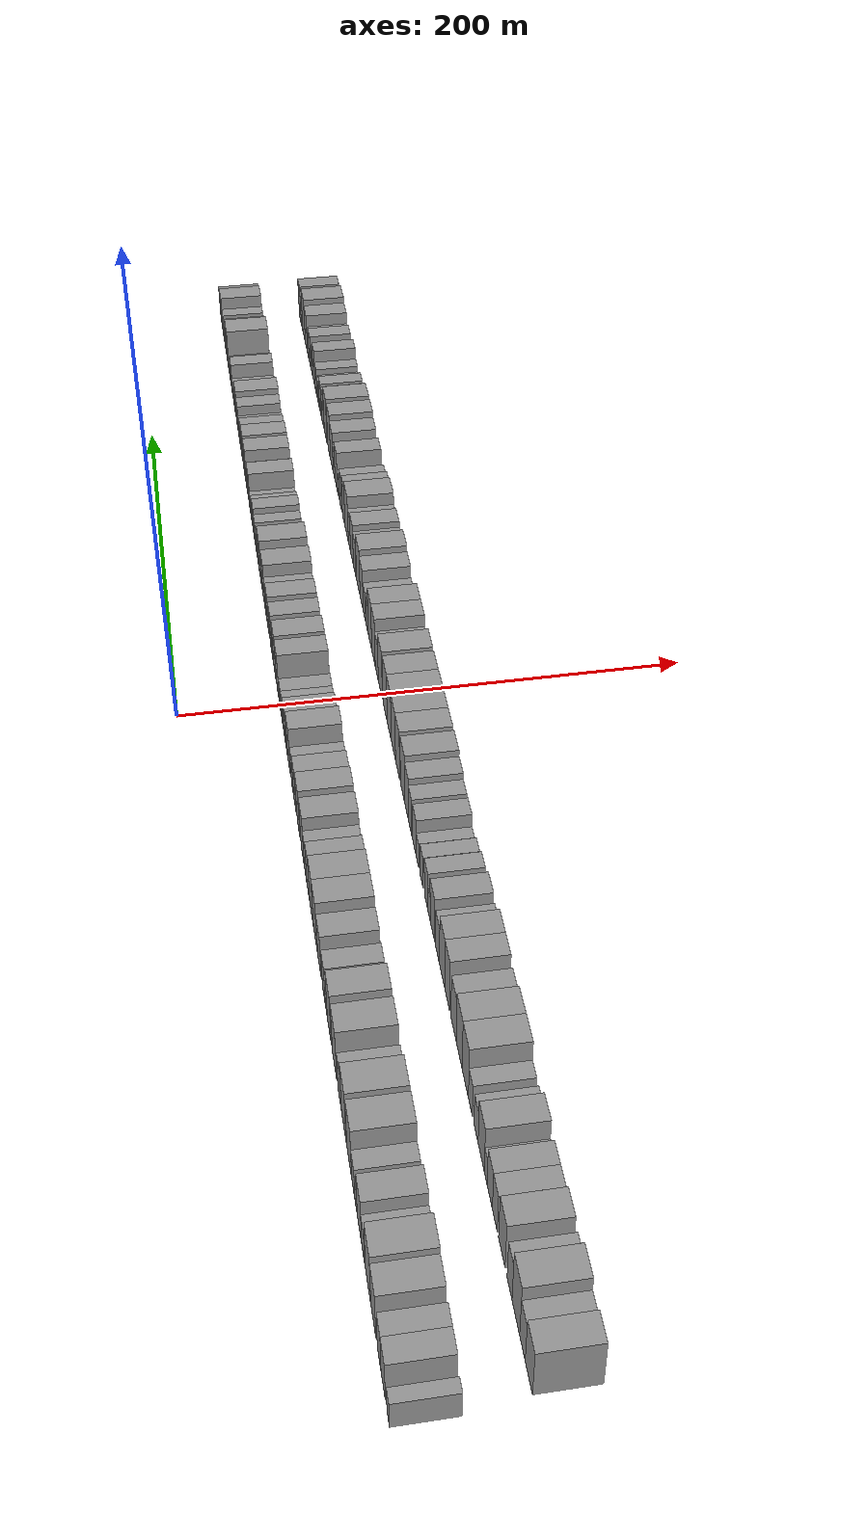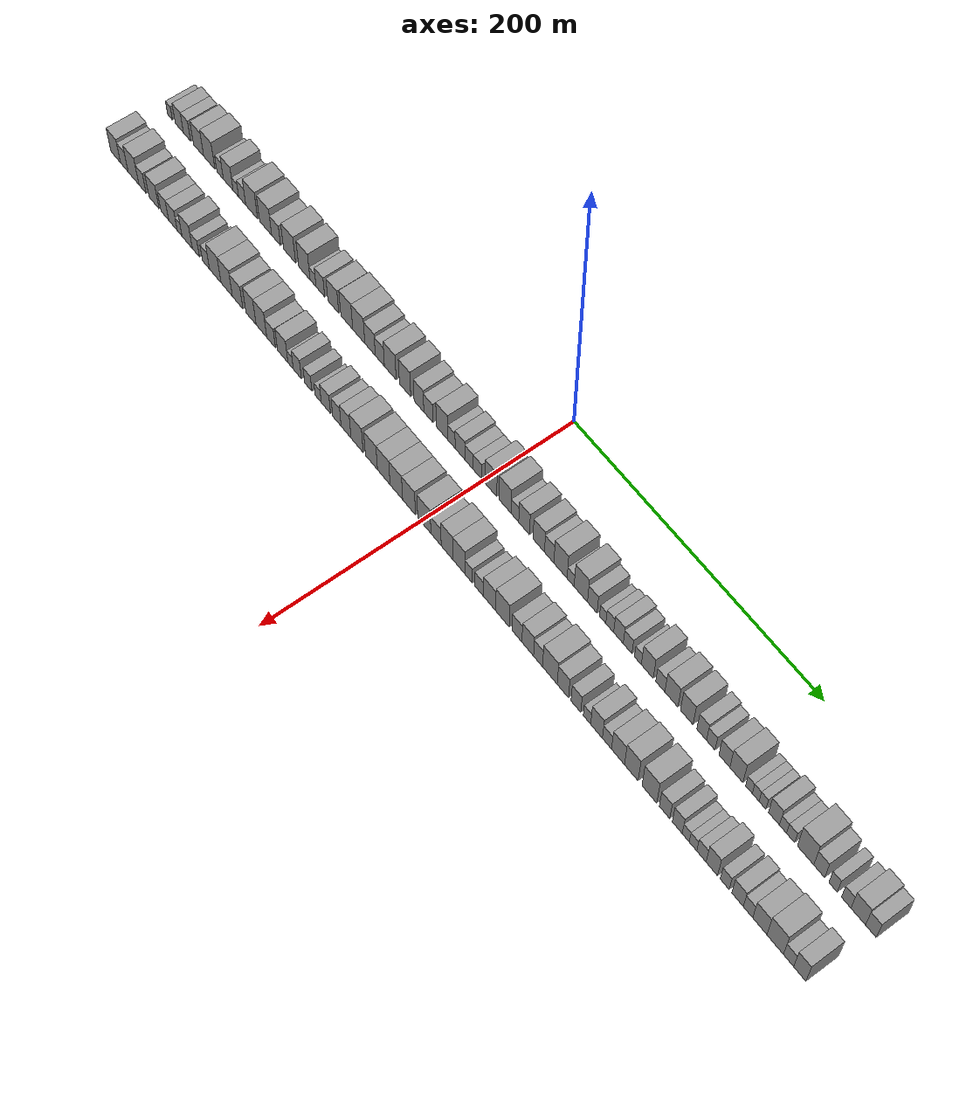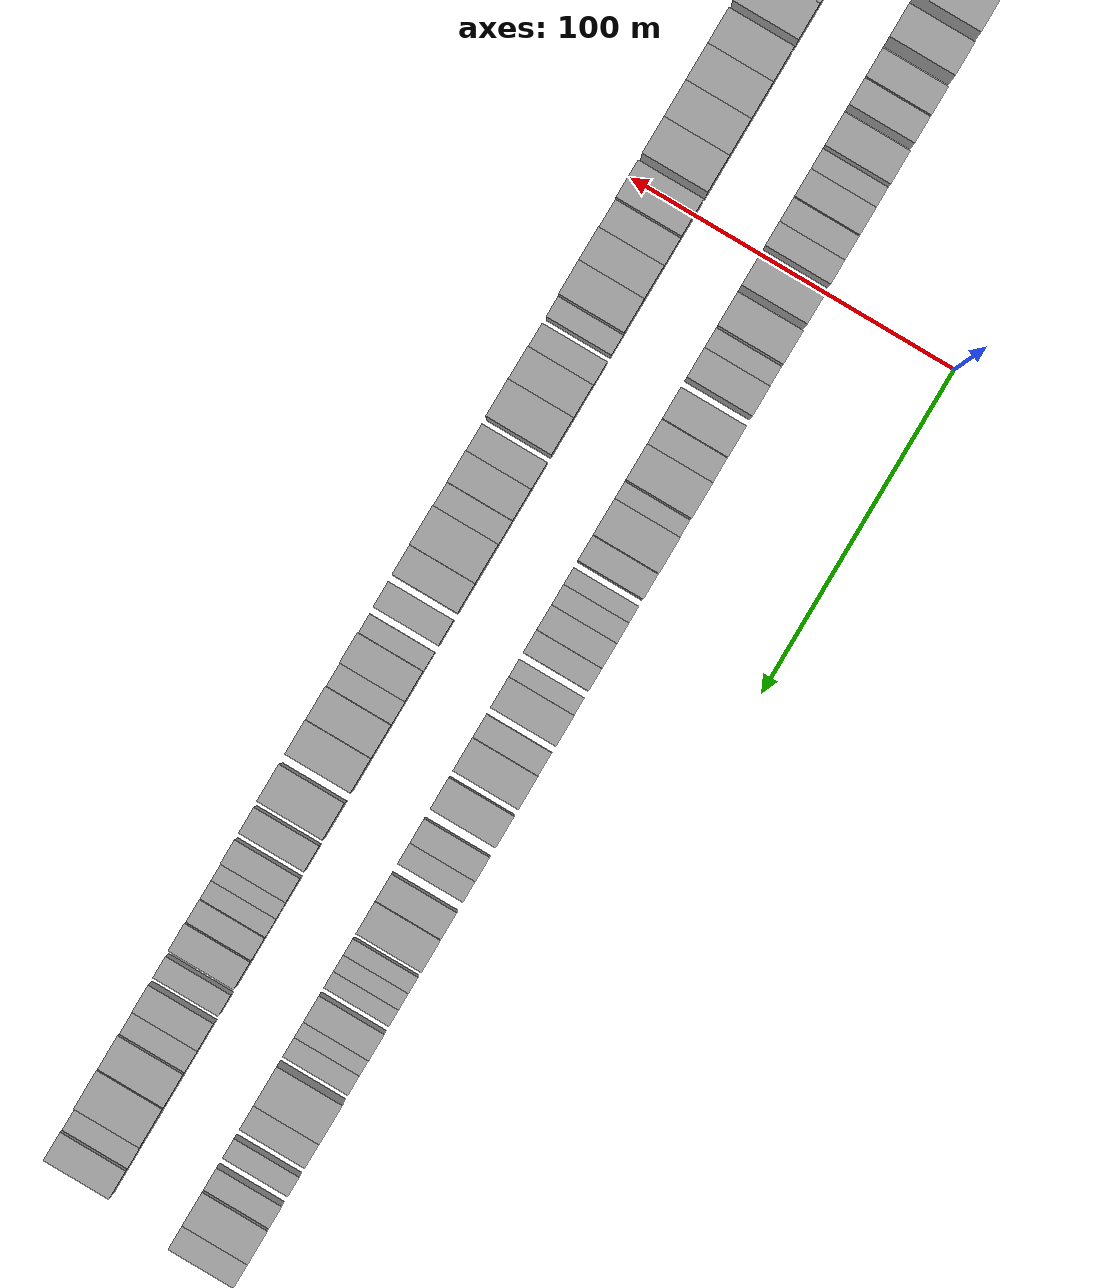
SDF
<sdf version="1.6">
 <world name="default">
  <scene>
   <sky><clouds><speed>12</speed></clouds></sky>
   <ambient>0.4 0.4 0.4 1</ambient>
   <background>0.7 0.7 0.7 1</background>
   <shadows>1</shadows>
  </scene>
  <gravity>0 0 -9.8066</gravity>
  <magnetic_field>6e-06 2.3e-05 -4.2e-05</magnetic_field>
  <physics default="0" name="default_physics" type="ode">
   <ode>
    <solver>
     <type>quick</type>
     <iters>10</iters>
     <sor>1.0</sor>
     <use_dynamic_moi_rescaling>0</use_dynamic_moi_rescaling>
    </solver>
    <constraints>
     <cfm>0</cfm>
     <erp>0.2</erp>
     <contact_max_correcting_vel>100</contact_max_correcting_vel>
     <contact_surface_layer>0.001</contact_surface_layer>
    </constraints>
   </ode>
   <max_step_size>0.004</max_step_size>
   <real_time_factor>1</real_time_factor>
   <real_time_update_rate>250</real_time_update_rate>
  </physics>
  <light name="sun" type="directional">
   <pose>0 0 10 0 0 0</pose>
   <diffuse>0.8 0.8 0.8 1</diffuse>
   <specular>0.2 0.2 0.2 1</specular>
   <attenuation>
    <range>1000</range>
    <constant>0.9</constant>
    <linear>0.01</linear>
    <quadratic>0.001</quadratic>
   </attenuation>
   <direction>-0.5 0.1 -0.9</direction>
  </light>
  <model name="building_1">
   <static>1</static>
   <pose>50.0000 -297.5331 0 0.000000 0.000000 0.000000</pose>
   <link name="link">
    <pose>0 0 6.00 0 0 0</pose>
    <collision name="collision"><geometry><box><size>20.0000 4.9339 12.0000</size></box></geometry></collision>
    <visual name="visual">
     <cast_shadows>0</cast_shadows>
     <geometry><box><size>20.0000 4.9339 12.0000</size></box></geometry>
     <material>
      <script>
       <uri>model://grey_wall/materials/scripts</uri>
       <uri>model://grey_wall/materials/textures</uri>
       <name>vrc/grey_wall</name>
      </script>
     </material>
    </visual>
   </link>
  </model>
  <model name="building_2">
   <static>1</static>
   <pose>50.0000 -287.8337 0 0.000000 0.000000 0.000000</pose>
   <link name="link">
    <pose>0 0 9.00 0 0 0</pose>
    <collision name="collision"><geometry><box><size>20.0000 8.4648 18.0000</size></box></geometry></collision>
    <visual name="visual">
     <cast_shadows>0</cast_shadows>
     <geometry><box><size>20.0000 8.4648 18.0000</size></box></geometry>
     <material>
      <script>
       <uri>model://grey_wall/materials/scripts</uri>
       <uri>model://grey_wall/materials/textures</uri>
       <name>vrc/grey_wall</name>
      </script>
     </material>
    </visual>
   </link>
  </model>
  <model name="building_3">
   <static>1</static>
   <pose>50.0000 -279.8977 0 0.000000 0.000000 0.000000</pose>
   <link name="link">
    <pose>0 0 9.00 0 0 0</pose>
    <collision name="collision"><geometry><box><size>20.0000 7.4073 18.0000</size></box></geometry></collision>
    <visual name="visual">
     <cast_shadows>0</cast_shadows>
     <geometry><box><size>20.0000 7.4073 18.0000</size></box></geometry>
     <material>
      <script>
       <uri>model://grey_wall/materials/scripts</uri>
       <uri>model://grey_wall/materials/textures</uri>
       <name>vrc/grey_wall</name>
      </script>
     </material>
    </visual>
   </link>
  </model>
  <model name="building_4">
   <static>1</static>
   <pose>50.0000 -268.0133 0 0.000000 0.000000 0.000000</pose>
   <link name="link">
    <pose>0 0 10.50 0 0 0</pose>
    <collision name="collision"><geometry><box><size>20.0000 10.3615 21.0000</size></box></geometry></collision>
    <visual name="visual">
     <cast_shadows>0</cast_shadows>
     <geometry><box><size>20.0000 10.3615 21.0000</size></box></geometry>
     <material>
      <script>
       <uri>model://grey_wall/materials/scripts</uri>
       <uri>model://grey_wall/materials/textures</uri>
       <name>vrc/grey_wall</name>
      </script>
     </material>
    </visual>
   </link>
  </model>
  <model name="building_5">
   <static>1</static>
   <pose>50.0000 -257.1095 0 0.000000 0.000000 0.000000</pose>
   <link name="link">
    <pose>0 0 12.00 0 0 0</pose>
    <collision name="collision"><geometry><box><size>20.0000 11.4461 24.0000</size></box></geometry></collision>
    <visual name="visual">
     <cast_shadows>0</cast_shadows>
     <geometry><box><size>20.0000 11.4461 24.0000</size></box></geometry>
     <material>
      <script>
       <uri>model://grey_wall/materials/scripts</uri>
       <uri>model://grey_wall/materials/textures</uri>
       <name>vrc/grey_wall</name>
      </script>
     </material>
    </visual>
   </link>
  </model>
  <model name="building_6">
   <static>1</static>
   <pose>50.0000 -246.1366 0 0.000000 0.000000 0.000000</pose>
   <link name="link">
    <pose>0 0 7.50 0 0 0</pose>
    <collision name="collision"><geometry><box><size>20.0000 6.4996 15.0000</size></box></geometry></collision>
    <visual name="visual">
     <cast_shadows>0</cast_shadows>
     <geometry><box><size>20.0000 6.4996 15.0000</size></box></geometry>
     <material>
      <script>
       <uri>model://grey_wall/materials/scripts</uri>
       <uri>model://grey_wall/materials/textures</uri>
       <name>vrc/grey_wall</name>
      </script>
     </material>
    </visual>
   </link>
  </model>
  <model name="building_7">
   <static>1</static>
   <pose>50.0000 -237.9815 0 0.000000 0.000000 0.000000</pose>
   <link name="link">
    <pose>0 0 10.50 0 0 0</pose>
    <collision name="collision"><geometry><box><size>20.0000 9.8106 21.0000</size></box></geometry></collision>
    <visual name="visual">
     <cast_shadows>0</cast_shadows>
     <geometry><box><size>20.0000 9.8106 21.0000</size></box></geometry>
     <material>
      <script>
       <uri>model://grey_wall/materials/scripts</uri>
       <uri>model://grey_wall/materials/textures</uri>
       <name>vrc/grey_wall</name>
      </script>
     </material>
    </visual>
   </link>
  </model>
  <model name="building_8">
   <static>1</static>
   <pose>50.0000 -230.3521 0 0.000000 0.000000 0.000000</pose>
   <link name="link">
    <pose>0 0 6.00 0 0 0</pose>
    <collision name="collision"><geometry><box><size>20.0000 5.4483 12.0000</size></box></geometry></collision>
    <visual name="visual">
     <cast_shadows>0</cast_shadows>
     <geometry><box><size>20.0000 5.4483 12.0000</size></box></geometry>
     <material>
      <script>
       <uri>model://grey_wall/materials/scripts</uri>
       <uri>model://grey_wall/materials/textures</uri>
       <name>vrc/grey_wall</name>
      </script>
     </material>
    </visual>
   </link>
  </model>
  <model name="building_9">
   <static>1</static>
   <pose>50.0000 -224.0166 0 0.000000 0.000000 0.000000</pose>
   <link name="link">
    <pose>0 0 7.50 0 0 0</pose>
    <collision name="collision"><geometry><box><size>20.0000 7.2227 15.0000</size></box></geometry></collision>
    <visual name="visual">
     <cast_shadows>0</cast_shadows>
     <geometry><box><size>20.0000 7.2227 15.0000</size></box></geometry>
     <material>
      <script>
       <uri>model://grey_wall/materials/scripts</uri>
       <uri>model://grey_wall/materials/textures</uri>
       <name>vrc/grey_wall</name>
      </script>
     </material>
    </visual>
   </link>
  </model>
  <model name="building_10">
   <static>1</static>
   <pose>50.0000 -214.5583 0 0.000000 0.000000 0.000000</pose>
   <link name="link">
    <pose>0 0 12.00 0 0 0</pose>
    <collision name="collision"><geometry><box><size>20.0000 11.6939 24.0000</size></box></geometry></collision>
    <visual name="visual">
     <cast_shadows>0</cast_shadows>
     <geometry><box><size>20.0000 11.6939 24.0000</size></box></geometry>
     <material>
      <script>
       <uri>model://grey_wall/materials/scripts</uri>
       <uri>model://grey_wall/materials/textures</uri>
       <name>vrc/grey_wall</name>
      </script>
     </material>
    </visual>
   </link>
  </model>
  <model name="building_11">
   <static>1</static>
   <pose>50.0000 -200.7927 0 0.000000 0.000000 0.000000</pose>
   <link name="link">
    <pose>0 0 12.00 0 0 0</pose>
    <collision name="collision"><geometry><box><size>20.0000 11.8374 24.0000</size></box></geometry></collision>
    <visual name="visual">
     <cast_shadows>0</cast_shadows>
     <geometry><box><size>20.0000 11.8374 24.0000</size></box></geometry>
     <material>
      <script>
       <uri>model://grey_wall/materials/scripts</uri>
       <uri>model://grey_wall/materials/textures</uri>
       <name>vrc/grey_wall</name>
      </script>
     </material>
    </visual>
   </link>
  </model>
  <model name="building_12">
   <static>1</static>
   <pose>50.0000 -190.5478 0 0.000000 0.000000 0.000000</pose>
   <link name="link">
    <pose>0 0 9.00 0 0 0</pose>
    <collision name="collision"><geometry><box><size>20.0000 8.6524 18.0000</size></box></geometry></collision>
    <visual name="visual">
     <cast_shadows>0</cast_shadows>
     <geometry><box><size>20.0000 8.6524 18.0000</size></box></geometry>
     <material>
      <script>
       <uri>model://grey_wall/materials/scripts</uri>
       <uri>model://grey_wall/materials/textures</uri>
       <name>vrc/grey_wall</name>
      </script>
     </material>
    </visual>
   </link>
  </model>
  <model name="building_13">
   <static>1</static>
   <pose>50.0000 -177.4273 0 0.000000 0.000000 0.000000</pose>
   <link name="link">
    <pose>0 0 12.00 0 0 0</pose>
    <collision name="collision"><geometry><box><size>20.0000 11.5886 24.0000</size></box></geometry></collision>
    <visual name="visual">
     <cast_shadows>0</cast_shadows>
     <geometry><box><size>20.0000 11.5886 24.0000</size></box></geometry>
     <material>
      <script>
       <uri>model://grey_wall/materials/scripts</uri>
       <uri>model://grey_wall/materials/textures</uri>
       <name>vrc/grey_wall</name>
      </script>
     </material>
    </visual>
   </link>
  </model>
  <model name="building_14">
   <static>1</static>
   <pose>50.0000 -163.1958 0 0.000000 0.000000 0.000000</pose>
   <link name="link">
    <pose>0 0 12.00 0 0 0</pose>
    <collision name="collision"><geometry><box><size>20.0000 10.8744 24.0000</size></box></geometry></collision>
    <visual name="visual">
     <cast_shadows>0</cast_shadows>
     <geometry><box><size>20.0000 10.8744 24.0000</size></box></geometry>
     <material>
      <script>
       <uri>model://grey_wall/materials/scripts</uri>
       <uri>model://grey_wall/materials/textures</uri>
       <name>vrc/grey_wall</name>
      </script>
     </material>
    </visual>
   </link>
  </model>
  <model name="building_15">
   <static>1</static>
   <pose>50.0000 -154.9076 0 0.000000 0.000000 0.000000</pose>
   <link name="link">
    <pose>0 0 6.00 0 0 0</pose>
    <collision name="collision"><geometry><box><size>20.0000 5.7019 12.0000</size></box></geometry></collision>
    <visual name="visual">
     <cast_shadows>0</cast_shadows>
     <geometry><box><size>20.0000 5.7019 12.0000</size></box></geometry>
     <material>
      <script>
       <uri>model://grey_wall/materials/scripts</uri>
       <uri>model://grey_wall/materials/textures</uri>
       <name>vrc/grey_wall</name>
      </script>
     </material>
    </visual>
   </link>
  </model>
  <model name="building_16">
   <static>1</static>
   <pose>50.0000 -147.9186 0 0.000000 0.000000 0.000000</pose>
   <link name="link">
    <pose>0 0 9.00 0 0 0</pose>
    <collision name="collision"><geometry><box><size>20.0000 8.2761 18.0000</size></box></geometry></collision>
    <visual name="visual">
     <cast_shadows>0</cast_shadows>
     <geometry><box><size>20.0000 8.2761 18.0000</size></box></geometry>
     <material>
      <script>
       <uri>model://grey_wall/materials/scripts</uri>
       <uri>model://grey_wall/materials/textures</uri>
       <name>vrc/grey_wall</name>
      </script>
     </material>
    </visual>
   </link>
  </model>
  <model name="building_17">
   <static>1</static>
   <pose>50.0000 -135.6512 0 0.000000 0.000000 0.000000</pose>
   <link name="link">
    <pose>0 0 10.50 0 0 0</pose>
    <collision name="collision"><geometry><box><size>20.0000 10.2588 21.0000</size></box></geometry></collision>
    <visual name="visual">
     <cast_shadows>0</cast_shadows>
     <geometry><box><size>20.0000 10.2588 21.0000</size></box></geometry>
     <material>
      <script>
       <uri>model://grey_wall/materials/scripts</uri>
       <uri>model://grey_wall/materials/textures</uri>
       <name>vrc/grey_wall</name>
      </script>
     </material>
    </visual>
   </link>
  </model>
  <model name="building_18">
   <static>1</static>
   <pose>50.0000 -122.9784 0 0.000000 0.000000 0.000000</pose>
   <link name="link">
    <pose>0 0 12.00 0 0 0</pose>
    <collision name="collision"><geometry><box><size>20.0000 11.0869 24.0000</size></box></geometry></collision>
    <visual name="visual">
     <cast_shadows>0</cast_shadows>
     <geometry><box><size>20.0000 11.0869 24.0000</size></box></geometry>
     <material>
      <script>
       <uri>model://grey_wall/materials/scripts</uri>
       <uri>model://grey_wall/materials/textures</uri>
       <name>vrc/grey_wall</name>
      </script>
     </material>
    </visual>
   </link>
  </model>
  <model name="building_19">
   <static>1</static>
   <pose>50.0000 -111.7870 0 0.000000 0.000000 0.000000</pose>
   <link name="link">
    <pose>0 0 12.00 0 0 0</pose>
    <collision name="collision"><geometry><box><size>20.0000 11.2959 24.0000</size></box></geometry></collision>
    <visual name="visual">
     <cast_shadows>0</cast_shadows>
     <geometry><box><size>20.0000 11.2959 24.0000</size></box></geometry>
     <material>
      <script>
       <uri>model://grey_wall/materials/scripts</uri>
       <uri>model://grey_wall/materials/textures</uri>
       <name>vrc/grey_wall</name>
      </script>
     </material>
    </visual>
   </link>
  </model>
  <model name="building_20">
   <static>1</static>
   <pose>50.0000 -101.3249 0 0.000000 0.000000 0.000000</pose>
   <link name="link">
    <pose>0 0 10.50 0 0 0</pose>
    <collision name="collision"><geometry><box><size>20.0000 9.6283 21.0000</size></box></geometry></collision>
    <visual name="visual">
     <cast_shadows>0</cast_shadows>
     <geometry><box><size>20.0000 9.6283 21.0000</size></box></geometry>
     <material>
      <script>
       <uri>model://grey_wall/materials/scripts</uri>
       <uri>model://grey_wall/materials/textures</uri>
       <name>vrc/grey_wall</name>
      </script>
     </material>
    </visual>
   </link>
  </model>
  <model name="building_21">
   <static>1</static>
   <pose>50.0000 -92.3364 0 0.000000 0.000000 0.000000</pose>
   <link name="link">
    <pose>0 0 9.00 0 0 0</pose>
    <collision name="collision"><geometry><box><size>20.0000 8.3488 18.0000</size></box></geometry></collision>
    <visual name="visual">
     <cast_shadows>0</cast_shadows>
     <geometry><box><size>20.0000 8.3488 18.0000</size></box></geometry>
     <material>
      <script>
       <uri>model://grey_wall/materials/scripts</uri>
       <uri>model://grey_wall/materials/textures</uri>
       <name>vrc/grey_wall</name>
      </script>
     </material>
    </visual>
   </link>
  </model>
  <model name="building_22">
   <static>1</static>
   <pose>50.0000 -82.8064 0 0.000000 0.000000 0.000000</pose>
   <link name="link">
    <pose>0 0 12.00 0 0 0</pose>
    <collision name="collision"><geometry><box><size>20.0000 10.7113 24.0000</size></box></geometry></collision>
    <visual name="visual">
     <cast_shadows>0</cast_shadows>
     <geometry><box><size>20.0000 10.7113 24.0000</size></box></geometry>
     <material>
      <script>
       <uri>model://grey_wall/materials/scripts</uri>
       <uri>model://grey_wall/materials/textures</uri>
       <name>vrc/grey_wall</name>
      </script>
     </material>
    </visual>
   </link>
  </model>
  <model name="building_23">
   <static>1</static>
   <pose>50.0000 -69.3587 0 0.000000 0.000000 0.000000</pose>
   <link name="link">
    <pose>0 0 12.00 0 0 0</pose>
    <collision name="collision"><geometry><box><size>20.0000 10.1841 24.0000</size></box></geometry></collision>
    <visual name="visual">
     <cast_shadows>0</cast_shadows>
     <geometry><box><size>20.0000 10.1841 24.0000</size></box></geometry>
     <material>
      <script>
       <uri>model://grey_wall/materials/scripts</uri>
       <uri>model://grey_wall/materials/textures</uri>
       <name>vrc/grey_wall</name>
      </script>
     </material>
    </visual>
   </link>
  </model>
  <model name="building_24">
   <static>1</static>
   <pose>50.0000 -56.8853 0 0.000000 0.000000 0.000000</pose>
   <link name="link">
    <pose>0 0 10.50 0 0 0</pose>
    <collision name="collision"><geometry><box><size>20.0000 8.7627 21.0000</size></box></geometry></collision>
    <visual name="visual">
     <cast_shadows>0</cast_shadows>
     <geometry><box><size>20.0000 8.7627 21.0000</size></box></geometry>
     <material>
      <script>
       <uri>model://grey_wall/materials/scripts</uri>
       <uri>model://grey_wall/materials/textures</uri>
       <name>vrc/grey_wall</name>
      </script>
     </material>
    </visual>
   </link>
  </model>
  <model name="building_25">
   <static>1</static>
   <pose>50.0000 -48.4280 0 0.000000 0.000000 0.000000</pose>
   <link name="link">
    <pose>0 0 9.00 0 0 0</pose>
    <collision name="collision"><geometry><box><size>20.0000 8.1518 18.0000</size></box></geometry></collision>
    <visual name="visual">
     <cast_shadows>0</cast_shadows>
     <geometry><box><size>20.0000 8.1518 18.0000</size></box></geometry>
     <material>
      <script>
       <uri>model://grey_wall/materials/scripts</uri>
       <uri>model://grey_wall/materials/textures</uri>
       <name>vrc/grey_wall</name>
      </script>
     </material>
    </visual>
   </link>
  </model>
  <model name="building_26">
   <static>1</static>
   <pose>50.0000 -36.2777 0 0.000000 0.000000 0.000000</pose>
   <link name="link">
    <pose>0 0 12.00 0 0 0</pose>
    <collision name="collision"><geometry><box><size>20.0000 10.1488 24.0000</size></box></geometry></collision>
    <visual name="visual">
     <cast_shadows>0</cast_shadows>
     <geometry><box><size>20.0000 10.1488 24.0000</size></box></geometry>
     <material>
      <script>
       <uri>model://grey_wall/materials/scripts</uri>
       <uri>model://grey_wall/materials/textures</uri>
       <name>vrc/grey_wall</name>
      </script>
     </material>
    </visual>
   </link>
  </model>
  <model name="building_27">
   <static>1</static>
   <pose>50.0000 -27.9706 0 0.000000 0.000000 0.000000</pose>
   <link name="link">
    <pose>0 0 7.50 0 0 0</pose>
    <collision name="collision"><geometry><box><size>20.0000 6.4655 15.0000</size></box></geometry></collision>
    <visual name="visual">
     <cast_shadows>0</cast_shadows>
     <geometry><box><size>20.0000 6.4655 15.0000</size></box></geometry>
     <material>
      <script>
       <uri>model://grey_wall/materials/scripts</uri>
       <uri>model://grey_wall/materials/textures</uri>
       <name>vrc/grey_wall</name>
      </script>
     </material>
    </visual>
   </link>
  </model>
  <model name="building_28">
   <static>1</static>
   <pose>50.0000 -20.5043 0 0.000000 0.000000 0.000000</pose>
   <link name="link">
    <pose>0 0 9.00 0 0 0</pose>
    <collision name="collision"><geometry><box><size>20.0000 8.4670 18.0000</size></box></geometry></collision>
    <visual name="visual">
     <cast_shadows>0</cast_shadows>
     <geometry><box><size>20.0000 8.4670 18.0000</size></box></geometry>
     <material>
      <script>
       <uri>model://grey_wall/materials/scripts</uri>
       <uri>model://grey_wall/materials/textures</uri>
       <name>vrc/grey_wall</name>
      </script>
     </material>
    </visual>
   </link>
  </model>
  <model name="building_29">
   <static>1</static>
   <pose>50.0000 -12.5937 0 0.000000 0.000000 0.000000</pose>
   <link name="link">
    <pose>0 0 7.50 0 0 0</pose>
    <collision name="collision"><geometry><box><size>20.0000 7.3543 15.0000</size></box></geometry></collision>
    <visual name="visual">
     <cast_shadows>0</cast_shadows>
     <geometry><box><size>20.0000 7.3543 15.0000</size></box></geometry>
     <material>
      <script>
       <uri>model://grey_wall/materials/scripts</uri>
       <uri>model://grey_wall/materials/textures</uri>
       <name>vrc/grey_wall</name>
      </script>
     </material>
    </visual>
   </link>
  </model>
  <model name="building_30">
   <static>1</static>
   <pose>50.0000 -5.2264 0 0.000000 0.000000 0.000000</pose>
   <link name="link">
    <pose>0 0 7.50 0 0 0</pose>
    <collision name="collision"><geometry><box><size>20.0000 7.3801 15.0000</size></box></geometry></collision>
    <visual name="visual">
     <cast_shadows>0</cast_shadows>
     <geometry><box><size>20.0000 7.3801 15.0000</size></box></geometry>
     <material>
      <script>
       <uri>model://grey_wall/materials/scripts</uri>
       <uri>model://grey_wall/materials/textures</uri>
       <name>vrc/grey_wall</name>
      </script>
     </material>
    </visual>
   </link>
  </model>
  <model name="building_31">
   <static>1</static>
   <pose>50.0000 6.4105 0 0.000000 0.000000 0.000000</pose>
   <link name="link">
    <pose>0 0 12.00 0 0 0</pose>
    <collision name="collision"><geometry><box><size>20.0000 9.8938 24.0000</size></box></geometry></collision>
    <visual name="visual">
     <cast_shadows>0</cast_shadows>
     <geometry><box><size>20.0000 9.8938 24.0000</size></box></geometry>
     <material>
      <script>
       <uri>model://grey_wall/materials/scripts</uri>
       <uri>model://grey_wall/materials/textures</uri>
       <name>vrc/grey_wall</name>
      </script>
     </material>
    </visual>
   </link>
  </model>
  <model name="building_32">
   <static>1</static>
   <pose>50.0000 18.5076 0 0.000000 0.000000 0.000000</pose>
   <link name="link">
    <pose>0 0 12.00 0 0 0</pose>
    <collision name="collision"><geometry><box><size>20.0000 10.3004 24.0000</size></box></geometry></collision>
    <visual name="visual">
     <cast_shadows>0</cast_shadows>
     <geometry><box><size>20.0000 10.3004 24.0000</size></box></geometry>
     <material>
      <script>
       <uri>model://grey_wall/materials/scripts</uri>
       <uri>model://grey_wall/materials/textures</uri>
       <name>vrc/grey_wall</name>
      </script>
     </material>
    </visual>
   </link>
  </model>
  <model name="building_33">
   <static>1</static>
   <pose>50.0000 26.8743 0 0.000000 0.000000 0.000000</pose>
   <link name="link">
    <pose>0 0 7.50 0 0 0</pose>
    <collision name="collision"><geometry><box><size>20.0000 6.4330 15.0000</size></box></geometry></collision>
    <visual name="visual">
     <cast_shadows>0</cast_shadows>
     <geometry><box><size>20.0000 6.4330 15.0000</size></box></geometry>
     <material>
      <script>
       <uri>model://grey_wall/materials/scripts</uri>
       <uri>model://grey_wall/materials/textures</uri>
       <name>vrc/grey_wall</name>
      </script>
     </material>
    </visual>
   </link>
  </model>
  <model name="building_34">
   <static>1</static>
   <pose>50.0000 34.6418 0 0.000000 0.000000 0.000000</pose>
   <link name="link">
    <pose>0 0 10.50 0 0 0</pose>
    <collision name="collision"><geometry><box><size>20.0000 9.1019 21.0000</size></box></geometry></collision>
    <visual name="visual">
     <cast_shadows>0</cast_shadows>
     <geometry><box><size>20.0000 9.1019 21.0000</size></box></geometry>
     <material>
      <script>
       <uri>model://grey_wall/materials/scripts</uri>
       <uri>model://grey_wall/materials/textures</uri>
       <name>vrc/grey_wall</name>
      </script>
     </material>
    </visual>
   </link>
  </model>
  <model name="building_35">
   <static>1</static>
   <pose>50.0000 46.9906 0 0.000000 0.000000 0.000000</pose>
   <link name="link">
    <pose>0 0 10.50 0 0 0</pose>
    <collision name="collision"><geometry><box><size>20.0000 9.5956 21.0000</size></box></geometry></collision>
    <visual name="visual">
     <cast_shadows>0</cast_shadows>
     <geometry><box><size>20.0000 9.5956 21.0000</size></box></geometry>
     <material>
      <script>
       <uri>model://grey_wall/materials/scripts</uri>
       <uri>model://grey_wall/materials/textures</uri>
       <name>vrc/grey_wall</name>
      </script>
     </material>
    </visual>
   </link>
  </model>
  <model name="building_36">
   <static>1</static>
   <pose>50.0000 55.7116 0 0.000000 0.000000 0.000000</pose>
   <link name="link">
    <pose>0 0 9.00 0 0 0</pose>
    <collision name="collision"><geometry><box><size>20.0000 7.8465 18.0000</size></box></geometry></collision>
    <visual name="visual">
     <cast_shadows>0</cast_shadows>
     <geometry><box><size>20.0000 7.8465 18.0000</size></box></geometry>
     <material>
      <script>
       <uri>model://grey_wall/materials/scripts</uri>
       <uri>model://grey_wall/materials/textures</uri>
       <name>vrc/grey_wall</name>
      </script>
     </material>
    </visual>
   </link>
  </model>
  <model name="building_37">
   <static>1</static>
   <pose>50.0000 65.1007 0 0.000000 0.000000 0.000000</pose>
   <link name="link">
    <pose>0 0 12.00 0 0 0</pose>
    <collision name="collision"><geometry><box><size>20.0000 10.9316 24.0000</size></box></geometry></collision>
    <visual name="visual">
     <cast_shadows>0</cast_shadows>
     <geometry><box><size>20.0000 10.9316 24.0000</size></box></geometry>
     <material>
      <script>
       <uri>model://grey_wall/materials/scripts</uri>
       <uri>model://grey_wall/materials/textures</uri>
       <name>vrc/grey_wall</name>
      </script>
     </material>
    </visual>
   </link>
  </model>
  <model name="building_38">
   <static>1</static>
   <pose>50.0000 73.4264 0 0.000000 0.000000 0.000000</pose>
   <link name="link">
    <pose>0 0 6.00 0 0 0</pose>
    <collision name="collision"><geometry><box><size>20.0000 5.7200 12.0000</size></box></geometry></collision>
    <visual name="visual">
     <cast_shadows>0</cast_shadows>
     <geometry><box><size>20.0000 5.7200 12.0000</size></box></geometry>
     <material>
      <script>
       <uri>model://grey_wall/materials/scripts</uri>
       <uri>model://grey_wall/materials/textures</uri>
       <name>vrc/grey_wall</name>
      </script>
     </material>
    </visual>
   </link>
  </model>
  <model name="building_39">
   <static>1</static>
   <pose>50.0000 81.7890 0 0.000000 0.000000 0.000000</pose>
   <link name="link">
    <pose>0 0 12.00 0 0 0</pose>
    <collision name="collision"><geometry><box><size>20.0000 11.0051 24.0000</size></box></geometry></collision>
    <visual name="visual">
     <cast_shadows>0</cast_shadows>
     <geometry><box><size>20.0000 11.0051 24.0000</size></box></geometry>
     <material>
      <script>
       <uri>model://grey_wall/materials/scripts</uri>
       <uri>model://grey_wall/materials/textures</uri>
       <name>vrc/grey_wall</name>
      </script>
     </material>
    </visual>
   </link>
  </model>
  <model name="building_40">
   <static>1</static>
   <pose>50.0000 91.1597 0 0.000000 0.000000 0.000000</pose>
   <link name="link">
    <pose>0 0 9.00 0 0 0</pose>
    <collision name="collision"><geometry><box><size>20.0000 7.7363 18.0000</size></box></geometry></collision>
    <visual name="visual">
     <cast_shadows>0</cast_shadows>
     <geometry><box><size>20.0000 7.7363 18.0000</size></box></geometry>
     <material>
      <script>
       <uri>model://grey_wall/materials/scripts</uri>
       <uri>model://grey_wall/materials/textures</uri>
       <name>vrc/grey_wall</name>
      </script>
     </material>
    </visual>
   </link>
  </model>
  <model name="building_41">
   <static>1</static>
   <pose>50.0000 99.6184 0 0.000000 0.000000 0.000000</pose>
   <link name="link">
    <pose>0 0 6.00 0 0 0</pose>
    <collision name="collision"><geometry><box><size>20.0000 5.1811 12.0000</size></box></geometry></collision>
    <visual name="visual">
     <cast_shadows>0</cast_shadows>
     <geometry><box><size>20.0000 5.1811 12.0000</size></box></geometry>
     <material>
      <script>
       <uri>model://grey_wall/materials/scripts</uri>
       <uri>model://grey_wall/materials/textures</uri>
       <name>vrc/grey_wall</name>
      </script>
     </material>
    </visual>
   </link>
  </model>
  <model name="building_42">
   <static>1</static>
   <pose>50.0000 105.3575 0 0.000000 0.000000 0.000000</pose>
   <link name="link">
    <pose>0 0 7.50 0 0 0</pose>
    <collision name="collision"><geometry><box><size>20.0000 6.2972 15.0000</size></box></geometry></collision>
    <visual name="visual">
     <cast_shadows>0</cast_shadows>
     <geometry><box><size>20.0000 6.2972 15.0000</size></box></geometry>
     <material>
      <script>
       <uri>model://grey_wall/materials/scripts</uri>
       <uri>model://grey_wall/materials/textures</uri>
       <name>vrc/grey_wall</name>
      </script>
     </material>
    </visual>
   </link>
  </model>
  <model name="building_43">
   <static>1</static>
   <pose>50.0000 112.3282 0 0.000000 0.000000 0.000000</pose>
   <link name="link">
    <pose>0 0 9.00 0 0 0</pose>
    <collision name="collision"><geometry><box><size>20.0000 7.6441 18.0000</size></box></geometry></collision>
    <visual name="visual">
     <cast_shadows>0</cast_shadows>
     <geometry><box><size>20.0000 7.6441 18.0000</size></box></geometry>
     <material>
      <script>
       <uri>model://grey_wall/materials/scripts</uri>
       <uri>model://grey_wall/materials/textures</uri>
       <name>vrc/grey_wall</name>
      </script>
     </material>
    </visual>
   </link>
  </model>
  <model name="building_44">
   <static>1</static>
   <pose>50.0000 119.6275 0 0.000000 0.000000 0.000000</pose>
   <link name="link">
    <pose>0 0 7.50 0 0 0</pose>
    <collision name="collision"><geometry><box><size>20.0000 6.9546 15.0000</size></box></geometry></collision>
    <visual name="visual">
     <cast_shadows>0</cast_shadows>
     <geometry><box><size>20.0000 6.9546 15.0000</size></box></geometry>
     <material>
      <script>
       <uri>model://grey_wall/materials/scripts</uri>
       <uri>model://grey_wall/materials/textures</uri>
       <name>vrc/grey_wall</name>
      </script>
     </material>
    </visual>
   </link>
  </model>
  <model name="building_45">
   <static>1</static>
   <pose>50.0000 127.7976 0 0.000000 0.000000 0.000000</pose>
   <link name="link">
    <pose>0 0 6.00 0 0 0</pose>
    <collision name="collision"><geometry><box><size>20.0000 5.3856 12.0000</size></box></geometry></collision>
    <visual name="visual">
     <cast_shadows>0</cast_shadows>
     <geometry><box><size>20.0000 5.3856 12.0000</size></box></geometry>
     <material>
      <script>
       <uri>model://grey_wall/materials/scripts</uri>
       <uri>model://grey_wall/materials/textures</uri>
       <name>vrc/grey_wall</name>
      </script>
     </material>
    </visual>
   </link>
  </model>
  <model name="building_46">
   <static>1</static>
   <pose>50.0000 135.2034 0 0.000000 0.000000 0.000000</pose>
   <link name="link">
    <pose>0 0 10.50 0 0 0</pose>
    <collision name="collision"><geometry><box><size>20.0000 9.4259 21.0000</size></box></geometry></collision>
    <visual name="visual">
     <cast_shadows>0</cast_shadows>
     <geometry><box><size>20.0000 9.4259 21.0000</size></box></geometry>
     <material>
      <script>
       <uri>model://grey_wall/materials/scripts</uri>
       <uri>model://grey_wall/materials/textures</uri>
       <name>vrc/grey_wall</name>
      </script>
     </material>
    </visual>
   </link>
  </model>
  <model name="building_47">
   <static>1</static>
   <pose>50.0000 145.4848 0 0.000000 0.000000 0.000000</pose>
   <link name="link">
    <pose>0 0 7.50 0 0 0</pose>
    <collision name="collision"><geometry><box><size>20.0000 7.1369 15.0000</size></box></geometry></collision>
    <visual name="visual">
     <cast_shadows>0</cast_shadows>
     <geometry><box><size>20.0000 7.1369 15.0000</size></box></geometry>
     <material>
      <script>
       <uri>model://grey_wall/materials/scripts</uri>
       <uri>model://grey_wall/materials/textures</uri>
       <name>vrc/grey_wall</name>
      </script>
     </material>
    </visual>
   </link>
  </model>
  <model name="building_48">
   <static>1</static>
   <pose>50.0000 154.1244 0 0.000000 0.000000 0.000000</pose>
   <link name="link">
    <pose>0 0 10.50 0 0 0</pose>
    <collision name="collision"><geometry><box><size>20.0000 10.1422 21.0000</size></box></geometry></collision>
    <visual name="visual">
     <cast_shadows>0</cast_shadows>
     <geometry><box><size>20.0000 10.1422 21.0000</size></box></geometry>
     <material>
      <script>
       <uri>model://grey_wall/materials/scripts</uri>
       <uri>model://grey_wall/materials/textures</uri>
       <name>vrc/grey_wall</name>
      </script>
     </material>
    </visual>
   </link>
  </model>
  <model name="building_49">
   <static>1</static>
   <pose>50.0000 166.0263 0 0.000000 0.000000 0.000000</pose>
   <link name="link">
    <pose>0 0 10.50 0 0 0</pose>
    <collision name="collision"><geometry><box><size>20.0000 9.6616 21.0000</size></box></geometry></collision>
    <visual name="visual">
     <cast_shadows>0</cast_shadows>
     <geometry><box><size>20.0000 9.6616 21.0000</size></box></geometry>
     <material>
      <script>
       <uri>model://grey_wall/materials/scripts</uri>
       <uri>model://grey_wall/materials/textures</uri>
       <name>vrc/grey_wall</name>
      </script>
     </material>
    </visual>
   </link>
  </model>
  <model name="building_50">
   <static>1</static>
   <pose>50.0000 177.5705 0 0.000000 0.000000 0.000000</pose>
   <link name="link">
    <pose>0 0 9.00 0 0 0</pose>
    <collision name="collision"><geometry><box><size>20.0000 7.4269 18.0000</size></box></geometry></collision>
    <visual name="visual">
     <cast_shadows>0</cast_shadows>
     <geometry><box><size>20.0000 7.4269 18.0000</size></box></geometry>
     <material>
      <script>
       <uri>model://grey_wall/materials/scripts</uri>
       <uri>model://grey_wall/materials/textures</uri>
       <name>vrc/grey_wall</name>
      </script>
     </material>
    </visual>
   </link>
  </model>
  <model name="building_51">
   <static>1</static>
   <pose>50.0000 184.5104 0 0.000000 0.000000 0.000000</pose>
   <link name="link">
    <pose>0 0 7.50 0 0 0</pose>
    <collision name="collision"><geometry><box><size>20.0000 6.4529 15.0000</size></box></geometry></collision>
    <visual name="visual">
     <cast_shadows>0</cast_shadows>
     <geometry><box><size>20.0000 6.4529 15.0000</size></box></geometry>
     <material>
      <script>
       <uri>model://grey_wall/materials/scripts</uri>
       <uri>model://grey_wall/materials/textures</uri>
       <name>vrc/grey_wall</name>
      </script>
     </material>
    </visual>
   </link>
  </model>
  <model name="building_52">
   <static>1</static>
   <pose>50.0000 194.8778 0 0.000000 0.000000 0.000000</pose>
   <link name="link">
    <pose>0 0 9.00 0 0 0</pose>
    <collision name="collision"><geometry><box><size>20.0000 8.2820 18.0000</size></box></geometry></collision>
    <visual name="visual">
     <cast_shadows>0</cast_shadows>
     <geometry><box><size>20.0000 8.2820 18.0000</size></box></geometry>
     <material>
      <script>
       <uri>model://grey_wall/materials/scripts</uri>
       <uri>model://grey_wall/materials/textures</uri>
       <name>vrc/grey_wall</name>
      </script>
     </material>
    </visual>
   </link>
  </model>
  <model name="building_53">
   <static>1</static>
   <pose>50.0000 203.9440 0 0.000000 0.000000 0.000000</pose>
   <link name="link">
    <pose>0 0 10.50 0 0 0</pose>
    <collision name="collision"><geometry><box><size>20.0000 9.8504 21.0000</size></box></geometry></collision>
    <visual name="visual">
     <cast_shadows>0</cast_shadows>
     <geometry><box><size>20.0000 9.8504 21.0000</size></box></geometry>
     <material>
      <script>
       <uri>model://grey_wall/materials/scripts</uri>
       <uri>model://grey_wall/materials/textures</uri>
       <name>vrc/grey_wall</name>
      </script>
     </material>
    </visual>
   </link>
  </model>
  <model name="building_54">
   <static>1</static>
   <pose>50.0000 213.3697 0 0.000000 0.000000 0.000000</pose>
   <link name="link">
    <pose>0 0 6.00 0 0 0</pose>
    <collision name="collision"><geometry><box><size>20.0000 5.0008 12.0000</size></box></geometry></collision>
    <visual name="visual">
     <cast_shadows>0</cast_shadows>
     <geometry><box><size>20.0000 5.0008 12.0000</size></box></geometry>
     <material>
      <script>
       <uri>model://grey_wall/materials/scripts</uri>
       <uri>model://grey_wall/materials/textures</uri>
       <name>vrc/grey_wall</name>
      </script>
     </material>
    </visual>
   </link>
  </model>
  <model name="building_55">
   <static>1</static>
   <pose>50.0000 218.3970 0 0.000000 0.000000 0.000000</pose>
   <link name="link">
    <pose>0 0 6.00 0 0 0</pose>
    <collision name="collision"><geometry><box><size>20.0000 5.0537 12.0000</size></box></geometry></collision>
    <visual name="visual">
     <cast_shadows>0</cast_shadows>
     <geometry><box><size>20.0000 5.0537 12.0000</size></box></geometry>
     <material>
      <script>
       <uri>model://grey_wall/materials/scripts</uri>
       <uri>model://grey_wall/materials/textures</uri>
       <name>vrc/grey_wall</name>
      </script>
     </material>
    </visual>
   </link>
  </model>
  <model name="building_56">
   <static>1</static>
   <pose>50.0000 223.4381 0 0.000000 0.000000 0.000000</pose>
   <link name="link">
    <pose>0 0 6.00 0 0 0</pose>
    <collision name="collision"><geometry><box><size>20.0000 5.0284 12.0000</size></box></geometry></collision>
    <visual name="visual">
     <cast_shadows>0</cast_shadows>
     <geometry><box><size>20.0000 5.0284 12.0000</size></box></geometry>
     <material>
      <script>
       <uri>model://grey_wall/materials/scripts</uri>
       <uri>model://grey_wall/materials/textures</uri>
       <name>vrc/grey_wall</name>
      </script>
     </material>
    </visual>
   </link>
  </model>
  <model name="building_57">
   <static>1</static>
   <pose>50.0000 231.9888 0 0.000000 0.000000 0.000000</pose>
   <link name="link">
    <pose>0 0 9.00 0 0 0</pose>
    <collision name="collision"><geometry><box><size>20.0000 8.0730 18.0000</size></box></geometry></collision>
    <visual name="visual">
     <cast_shadows>0</cast_shadows>
     <geometry><box><size>20.0000 8.0730 18.0000</size></box></geometry>
     <material>
      <script>
       <uri>model://grey_wall/materials/scripts</uri>
       <uri>model://grey_wall/materials/textures</uri>
       <name>vrc/grey_wall</name>
      </script>
     </material>
    </visual>
   </link>
  </model>
  <model name="building_58">
   <static>1</static>
   <pose>50.0000 238.5985 0 0.000000 0.000000 0.000000</pose>
   <link name="link">
    <pose>0 0 6.00 0 0 0</pose>
    <collision name="collision"><geometry><box><size>20.0000 5.1465 12.0000</size></box></geometry></collision>
    <visual name="visual">
     <cast_shadows>0</cast_shadows>
     <geometry><box><size>20.0000 5.1465 12.0000</size></box></geometry>
     <material>
      <script>
       <uri>model://grey_wall/materials/scripts</uri>
       <uri>model://grey_wall/materials/textures</uri>
       <name>vrc/grey_wall</name>
      </script>
     </material>
    </visual>
   </link>
  </model>
  <model name="building_59">
   <static>1</static>
   <pose>50.0000 244.1406 0 0.000000 0.000000 0.000000</pose>
   <link name="link">
    <pose>0 0 6.00 0 0 0</pose>
    <collision name="collision"><geometry><box><size>20.0000 5.9376 12.0000</size></box></geometry></collision>
    <visual name="visual">
     <cast_shadows>0</cast_shadows>
     <geometry><box><size>20.0000 5.9376 12.0000</size></box></geometry>
     <material>
      <script>
       <uri>model://grey_wall/materials/scripts</uri>
       <uri>model://grey_wall/materials/textures</uri>
       <name>vrc/grey_wall</name>
      </script>
     </material>
    </visual>
   </link>
  </model>
  <model name="building_60">
   <static>1</static>
   <pose>50.0000 255.0784 0 0.000000 0.000000 0.000000</pose>
   <link name="link">
    <pose>0 0 12.00 0 0 0</pose>
    <collision name="collision"><geometry><box><size>20.0000 11.9380 24.0000</size></box></geometry></collision>
    <visual name="visual">
     <cast_shadows>0</cast_shadows>
     <geometry><box><size>20.0000 11.9380 24.0000</size></box></geometry>
     <material>
      <script>
       <uri>model://grey_wall/materials/scripts</uri>
       <uri>model://grey_wall/materials/textures</uri>
       <name>vrc/grey_wall</name>
      </script>
     </material>
    </visual>
   </link>
  </model>
  <model name="building_61">
   <static>1</static>
   <pose>50.0000 264.9661 0 0.000000 0.000000 0.000000</pose>
   <link name="link">
    <pose>0 0 9.00 0 0 0</pose>
    <collision name="collision"><geometry><box><size>20.0000 7.8374 18.0000</size></box></geometry></collision>
    <visual name="visual">
     <cast_shadows>0</cast_shadows>
     <geometry><box><size>20.0000 7.8374 18.0000</size></box></geometry>
     <material>
      <script>
       <uri>model://grey_wall/materials/scripts</uri>
       <uri>model://grey_wall/materials/textures</uri>
       <name>vrc/grey_wall</name>
      </script>
     </material>
    </visual>
   </link>
  </model>
  <model name="building_62">
   <static>1</static>
   <pose>50.0000 274.8857 0 0.000000 0.000000 0.000000</pose>
   <link name="link">
    <pose>0 0 7.50 0 0 0</pose>
    <collision name="collision"><geometry><box><size>20.0000 6.0018 15.0000</size></box></geometry></collision>
    <visual name="visual">
     <cast_shadows>0</cast_shadows>
     <geometry><box><size>20.0000 6.0018 15.0000</size></box></geometry>
     <material>
      <script>
       <uri>model://grey_wall/materials/scripts</uri>
       <uri>model://grey_wall/materials/textures</uri>
       <name>vrc/grey_wall</name>
      </script>
     </material>
    </visual>
   </link>
  </model>
  <model name="building_63">
   <static>1</static>
   <pose>50.0000 284.2637 0 0.000000 0.000000 0.000000</pose>
   <link name="link">
    <pose>0 0 7.50 0 0 0</pose>
    <collision name="collision"><geometry><box><size>20.0000 6.7541 15.0000</size></box></geometry></collision>
    <visual name="visual">
     <cast_shadows>0</cast_shadows>
     <geometry><box><size>20.0000 6.7541 15.0000</size></box></geometry>
     <material>
      <script>
       <uri>model://grey_wall/materials/scripts</uri>
       <uri>model://grey_wall/materials/textures</uri>
       <name>vrc/grey_wall</name>
      </script>
     </material>
    </visual>
   </link>
  </model>
  <model name="building_64">
   <static>1</static>
   <pose>50.0000 292.7932 0 0.000000 0.000000 0.000000</pose>
   <link name="link">
    <pose>0 0 10.50 0 0 0</pose>
    <collision name="collision"><geometry><box><size>20.0000 10.3050 21.0000</size></box></geometry></collision>
    <visual name="visual">
     <cast_shadows>0</cast_shadows>
     <geometry><box><size>20.0000 10.3050 21.0000</size></box></geometry>
     <material>
      <script>
       <uri>model://grey_wall/materials/scripts</uri>
       <uri>model://grey_wall/materials/textures</uri>
       <name>vrc/grey_wall</name>
      </script>
     </material>
    </visual>
   </link>
  </model>
  <model name="building_65">
   <static>1</static>
   <pose>50.0000 301.7156 0 0.000000 0.000000 0.000000</pose>
   <link name="link">
    <pose>0 0 9.00 0 0 0</pose>
    <collision name="collision"><geometry><box><size>20.0000 7.5399 18.0000</size></box></geometry></collision>
    <visual name="visual">
     <cast_shadows>0</cast_shadows>
     <geometry><box><size>20.0000 7.5399 18.0000</size></box></geometry>
     <material>
      <script>
       <uri>model://grey_wall/materials/scripts</uri>
       <uri>model://grey_wall/materials/textures</uri>
       <name>vrc/grey_wall</name>
      </script>
     </material>
    </visual>
   </link>
  </model>
  <model name="building_66">
   <static>1</static>
   <pose>90.0000 -291.9451 0 0.000000 0.000000 0.000000</pose>
   <link name="link">
    <pose>0 0 10.50 0 0 0</pose>
    <collision name="collision"><geometry><box><size>20.0000 10.1097 21.0000</size></box></geometry></collision>
    <visual name="visual">
     <cast_shadows>0</cast_shadows>
     <geometry><box><size>20.0000 10.1097 21.0000</size></box></geometry>
     <material>
      <script>
       <uri>model://grey_wall/materials/scripts</uri>
       <uri>model://grey_wall/materials/textures</uri>
       <name>vrc/grey_wall</name>
      </script>
     </material>
    </visual>
   </link>
  </model>
  <model name="building_67">
   <static>1</static>
   <pose>90.0000 -282.9284 0 0.000000 0.000000 0.000000</pose>
   <link name="link">
    <pose>0 0 9.00 0 0 0</pose>
    <collision name="collision"><geometry><box><size>20.0000 7.9237 18.0000</size></box></geometry></collision>
    <visual name="visual">
     <cast_shadows>0</cast_shadows>
     <geometry><box><size>20.0000 7.9237 18.0000</size></box></geometry>
     <material>
      <script>
       <uri>model://grey_wall/materials/scripts</uri>
       <uri>model://grey_wall/materials/textures</uri>
       <name>vrc/grey_wall</name>
      </script>
     </material>
    </visual>
   </link>
  </model>
  <model name="building_68">
   <static>1</static>
   <pose>90.0000 -273.3744 0 0.000000 0.000000 0.000000</pose>
   <link name="link">
    <pose>0 0 12.00 0 0 0</pose>
    <collision name="collision"><geometry><box><size>20.0000 11.1841 24.0000</size></box></geometry></collision>
    <visual name="visual">
     <cast_shadows>0</cast_shadows>
     <geometry><box><size>20.0000 11.1841 24.0000</size></box></geometry>
     <material>
      <script>
       <uri>model://grey_wall/materials/scripts</uri>
       <uri>model://grey_wall/materials/textures</uri>
       <name>vrc/grey_wall</name>
      </script>
     </material>
    </visual>
   </link>
  </model>
  <model name="building_69">
   <static>1</static>
   <pose>90.0000 -264.0780 0 0.000000 0.000000 0.000000</pose>
   <link name="link">
    <pose>0 0 9.00 0 0 0</pose>
    <collision name="collision"><geometry><box><size>20.0000 7.4088 18.0000</size></box></geometry></collision>
    <visual name="visual">
     <cast_shadows>0</cast_shadows>
     <geometry><box><size>20.0000 7.4088 18.0000</size></box></geometry>
     <material>
      <script>
       <uri>model://grey_wall/materials/scripts</uri>
       <uri>model://grey_wall/materials/textures</uri>
       <name>vrc/grey_wall</name>
      </script>
     </material>
    </visual>
   </link>
  </model>
  <model name="building_70">
   <static>1</static>
   <pose>90.0000 -252.2582 0 0.000000 0.000000 0.000000</pose>
   <link name="link">
    <pose>0 0 10.50 0 0 0</pose>
    <collision name="collision"><geometry><box><size>20.0000 10.2306 21.0000</size></box></geometry></collision>
    <visual name="visual">
     <cast_shadows>0</cast_shadows>
     <geometry><box><size>20.0000 10.2306 21.0000</size></box></geometry>
     <material>
      <script>
       <uri>model://grey_wall/materials/scripts</uri>
       <uri>model://grey_wall/materials/textures</uri>
       <name>vrc/grey_wall</name>
      </script>
     </material>
    </visual>
   </link>
  </model>
  <model name="building_71">
   <static>1</static>
   <pose>90.0000 -241.2376 0 0.000000 0.000000 0.000000</pose>
   <link name="link">
    <pose>0 0 9.00 0 0 0</pose>
    <collision name="collision"><geometry><box><size>20.0000 7.8106 18.0000</size></box></geometry></collision>
    <visual name="visual">
     <cast_shadows>0</cast_shadows>
     <geometry><box><size>20.0000 7.8106 18.0000</size></box></geometry>
     <material>
      <script>
       <uri>model://grey_wall/materials/scripts</uri>
       <uri>model://grey_wall/materials/textures</uri>
       <name>vrc/grey_wall</name>
      </script>
     </material>
    </visual>
   </link>
  </model>
  <model name="building_72">
   <static>1</static>
   <pose>90.0000 -233.0132 0 0.000000 0.000000 0.000000</pose>
   <link name="link">
    <pose>0 0 9.00 0 0 0</pose>
    <collision name="collision"><geometry><box><size>20.0000 8.6383 18.0000</size></box></geometry></collision>
    <visual name="visual">
     <cast_shadows>0</cast_shadows>
     <geometry><box><size>20.0000 8.6383 18.0000</size></box></geometry>
     <material>
      <script>
       <uri>model://grey_wall/materials/scripts</uri>
       <uri>model://grey_wall/materials/textures</uri>
       <name>vrc/grey_wall</name>
      </script>
     </material>
    </visual>
   </link>
  </model>
  <model name="building_73">
   <static>1</static>
   <pose>90.0000 -226.2843 0 0.000000 0.000000 0.000000</pose>
   <link name="link">
    <pose>0 0 6.00 0 0 0</pose>
    <collision name="collision"><geometry><box><size>20.0000 4.8194 12.0000</size></box></geometry></collision>
    <visual name="visual">
     <cast_shadows>0</cast_shadows>
     <geometry><box><size>20.0000 4.8194 12.0000</size></box></geometry>
     <material>
      <script>
       <uri>model://grey_wall/materials/scripts</uri>
       <uri>model://grey_wall/materials/textures</uri>
       <name>vrc/grey_wall</name>
      </script>
     </material>
    </visual>
   </link>
  </model>
  <model name="building_74">
   <static>1</static>
   <pose>90.0000 -218.7127 0 0.000000 0.000000 0.000000</pose>
   <link name="link">
    <pose>0 0 10.50 0 0 0</pose>
    <collision name="collision"><geometry><box><size>20.0000 10.3237 21.0000</size></box></geometry></collision>
    <visual name="visual">
     <cast_shadows>0</cast_shadows>
     <geometry><box><size>20.0000 10.3237 21.0000</size></box></geometry>
     <material>
      <script>
       <uri>model://grey_wall/materials/scripts</uri>
       <uri>model://grey_wall/materials/textures</uri>
       <name>vrc/grey_wall</name>
      </script>
     </material>
    </visual>
   </link>
  </model>
  <model name="building_75">
   <static>1</static>
   <pose>90.0000 -209.9552 0 0.000000 0.000000 0.000000</pose>
   <link name="link">
    <pose>0 0 7.50 0 0 0</pose>
    <collision name="collision"><geometry><box><size>20.0000 7.1914 15.0000</size></box></geometry></collision>
    <visual name="visual">
     <cast_shadows>0</cast_shadows>
     <geometry><box><size>20.0000 7.1914 15.0000</size></box></geometry>
     <material>
      <script>
       <uri>model://grey_wall/materials/scripts</uri>
       <uri>model://grey_wall/materials/textures</uri>
       <name>vrc/grey_wall</name>
      </script>
     </material>
    </visual>
   </link>
  </model>
  <model name="building_76">
   <static>1</static>
   <pose>90.0000 -199.8760 0 0.000000 0.000000 0.000000</pose>
   <link name="link">
    <pose>0 0 7.50 0 0 0</pose>
    <collision name="collision"><geometry><box><size>20.0000 6.9670 15.0000</size></box></geometry></collision>
    <visual name="visual">
     <cast_shadows>0</cast_shadows>
     <geometry><box><size>20.0000 6.9670 15.0000</size></box></geometry>
     <material>
      <script>
       <uri>model://grey_wall/materials/scripts</uri>
       <uri>model://grey_wall/materials/textures</uri>
       <name>vrc/grey_wall</name>
      </script>
     </material>
    </visual>
   </link>
  </model>
  <model name="building_77">
   <static>1</static>
   <pose>90.0000 -190.7588 0 0.000000 0.000000 0.000000</pose>
   <link name="link">
    <pose>0 0 12.00 0 0 0</pose>
    <collision name="collision"><geometry><box><size>20.0000 11.2673 24.0000</size></box></geometry></collision>
    <visual name="visual">
     <cast_shadows>0</cast_shadows>
     <geometry><box><size>20.0000 11.2673 24.0000</size></box></geometry>
     <material>
      <script>
       <uri>model://grey_wall/materials/scripts</uri>
       <uri>model://grey_wall/materials/textures</uri>
       <name>vrc/grey_wall</name>
      </script>
     </material>
    </visual>
   </link>
  </model>
  <model name="building_78">
   <static>1</static>
   <pose>90.0000 -179.5299 0 0.000000 0.000000 0.000000</pose>
   <link name="link">
    <pose>0 0 12.00 0 0 0</pose>
    <collision name="collision"><geometry><box><size>20.0000 11.1906 24.0000</size></box></geometry></collision>
    <visual name="visual">
     <cast_shadows>0</cast_shadows>
     <geometry><box><size>20.0000 11.1906 24.0000</size></box></geometry>
     <material>
      <script>
       <uri>model://grey_wall/materials/scripts</uri>
       <uri>model://grey_wall/materials/textures</uri>
       <name>vrc/grey_wall</name>
      </script>
     </material>
    </visual>
   </link>
  </model>
  <model name="building_79">
   <static>1</static>
   <pose>90.0000 -168.8493 0 0.000000 0.000000 0.000000</pose>
   <link name="link">
    <pose>0 0 10.50 0 0 0</pose>
    <collision name="collision"><geometry><box><size>20.0000 10.1705 21.0000</size></box></geometry></collision>
    <visual name="visual">
     <cast_shadows>0</cast_shadows>
     <geometry><box><size>20.0000 10.1705 21.0000</size></box></geometry>
     <material>
      <script>
       <uri>model://grey_wall/materials/scripts</uri>
       <uri>model://grey_wall/materials/textures</uri>
       <name>vrc/grey_wall</name>
      </script>
     </material>
    </visual>
   </link>
  </model>
  <model name="building_80">
   <static>1</static>
   <pose>90.0000 -155.8895 0 0.000000 0.000000 0.000000</pose>
   <link name="link">
    <pose>0 0 12.00 0 0 0</pose>
    <collision name="collision"><geometry><box><size>20.0000 9.7491 24.0000</size></box></geometry></collision>
    <visual name="visual">
     <cast_shadows>0</cast_shadows>
     <geometry><box><size>20.0000 9.7491 24.0000</size></box></geometry>
     <material>
      <script>
       <uri>model://grey_wall/materials/scripts</uri>
       <uri>model://grey_wall/materials/textures</uri>
       <name>vrc/grey_wall</name>
      </script>
     </material>
    </visual>
   </link>
  </model>
  <model name="building_81">
   <static>1</static>
   <pose>90.0000 -145.8868 0 0.000000 0.000000 0.000000</pose>
   <link name="link">
    <pose>0 0 12.00 0 0 0</pose>
    <collision name="collision"><geometry><box><size>20.0000 10.2561 24.0000</size></box></geometry></collision>
    <visual name="visual">
     <cast_shadows>0</cast_shadows>
     <geometry><box><size>20.0000 10.2561 24.0000</size></box></geometry>
     <material>
      <script>
       <uri>model://grey_wall/materials/scripts</uri>
       <uri>model://grey_wall/materials/textures</uri>
       <name>vrc/grey_wall</name>
      </script>
     </material>
    </visual>
   </link>
  </model>
  <model name="building_82">
   <static>1</static>
   <pose>90.0000 -136.6373 0 0.000000 0.000000 0.000000</pose>
   <link name="link">
    <pose>0 0 9.00 0 0 0</pose>
    <collision name="collision"><geometry><box><size>20.0000 8.2430 18.0000</size></box></geometry></collision>
    <visual name="visual">
     <cast_shadows>0</cast_shadows>
     <geometry><box><size>20.0000 8.2430 18.0000</size></box></geometry>
     <material>
      <script>
       <uri>model://grey_wall/materials/scripts</uri>
       <uri>model://grey_wall/materials/textures</uri>
       <name>vrc/grey_wall</name>
      </script>
     </material>
    </visual>
   </link>
  </model>
  <model name="building_83">
   <static>1</static>
   <pose>90.0000 -125.5935 0 0.000000 0.000000 0.000000</pose>
   <link name="link">
    <pose>0 0 10.50 0 0 0</pose>
    <collision name="collision"><geometry><box><size>20.0000 9.8446 21.0000</size></box></geometry></collision>
    <visual name="visual">
     <cast_shadows>0</cast_shadows>
     <geometry><box><size>20.0000 9.8446 21.0000</size></box></geometry>
     <material>
      <script>
       <uri>model://grey_wall/materials/scripts</uri>
       <uri>model://grey_wall/materials/textures</uri>
       <name>vrc/grey_wall</name>
      </script>
     </material>
    </visual>
   </link>
  </model>
  <model name="building_84">
   <static>1</static>
   <pose>90.0000 -118.1962 0 0.000000 0.000000 0.000000</pose>
   <link name="link">
    <pose>0 0 6.00 0 0 0</pose>
    <collision name="collision"><geometry><box><size>20.0000 4.9500 12.0000</size></box></geometry></collision>
    <visual name="visual">
     <cast_shadows>0</cast_shadows>
     <geometry><box><size>20.0000 4.9500 12.0000</size></box></geometry>
     <material>
      <script>
       <uri>model://grey_wall/materials/scripts</uri>
       <uri>model://grey_wall/materials/textures</uri>
       <name>vrc/grey_wall</name>
      </script>
     </material>
    </visual>
   </link>
  </model>
  <model name="building_85">
   <static>1</static>
   <pose>90.0000 -111.8873 0 0.000000 0.000000 0.000000</pose>
   <link name="link">
    <pose>0 0 9.00 0 0 0</pose>
    <collision name="collision"><geometry><box><size>20.0000 7.6678 18.0000</size></box></geometry></collision>
    <visual name="visual">
     <cast_shadows>0</cast_shadows>
     <geometry><box><size>20.0000 7.6678 18.0000</size></box></geometry>
     <material>
      <script>
       <uri>model://grey_wall/materials/scripts</uri>
       <uri>model://grey_wall/materials/textures</uri>
       <name>vrc/grey_wall</name>
      </script>
     </material>
    </visual>
   </link>
  </model>
  <model name="building_86">
   <static>1</static>
   <pose>90.0000 -101.6432 0 0.000000 0.000000 0.000000</pose>
   <link name="link">
    <pose>0 0 7.50 0 0 0</pose>
    <collision name="collision"><geometry><box><size>20.0000 6.8204 15.0000</size></box></geometry></collision>
    <visual name="visual">
     <cast_shadows>0</cast_shadows>
     <geometry><box><size>20.0000 6.8204 15.0000</size></box></geometry>
     <material>
      <script>
       <uri>model://grey_wall/materials/scripts</uri>
       <uri>model://grey_wall/materials/textures</uri>
       <name>vrc/grey_wall</name>
      </script>
     </material>
    </visual>
   </link>
  </model>
  <model name="building_87">
   <static>1</static>
   <pose>90.0000 -92.4366 0 0.000000 0.000000 0.000000</pose>
   <link name="link">
    <pose>0 0 6.00 0 0 0</pose>
    <collision name="collision"><geometry><box><size>20.0000 5.5929 12.0000</size></box></geometry></collision>
    <visual name="visual">
     <cast_shadows>0</cast_shadows>
     <geometry><box><size>20.0000 5.5929 12.0000</size></box></geometry>
     <material>
      <script>
       <uri>model://grey_wall/materials/scripts</uri>
       <uri>model://grey_wall/materials/textures</uri>
       <name>vrc/grey_wall</name>
      </script>
     </material>
    </visual>
   </link>
  </model>
  <model name="building_88">
   <static>1</static>
   <pose>90.0000 -85.3417 0 0.000000 0.000000 0.000000</pose>
   <link name="link">
    <pose>0 0 9.00 0 0 0</pose>
    <collision name="collision"><geometry><box><size>20.0000 8.5969 18.0000</size></box></geometry></collision>
    <visual name="visual">
     <cast_shadows>0</cast_shadows>
     <geometry><box><size>20.0000 8.5969 18.0000</size></box></geometry>
     <material>
      <script>
       <uri>model://grey_wall/materials/scripts</uri>
       <uri>model://grey_wall/materials/textures</uri>
       <name>vrc/grey_wall</name>
      </script>
     </material>
    </visual>
   </link>
  </model>
  <model name="building_89">
   <static>1</static>
   <pose>90.0000 -75.1977 0 0.000000 0.000000 0.000000</pose>
   <link name="link">
    <pose>0 0 9.00 0 0 0</pose>
    <collision name="collision"><geometry><box><size>20.0000 7.6912 18.0000</size></box></geometry></collision>
    <visual name="visual">
     <cast_shadows>0</cast_shadows>
     <geometry><box><size>20.0000 7.6912 18.0000</size></box></geometry>
     <material>
      <script>
       <uri>model://grey_wall/materials/scripts</uri>
       <uri>model://grey_wall/materials/textures</uri>
       <name>vrc/grey_wall</name>
      </script>
     </material>
    </visual>
   </link>
  </model>
  <model name="building_90">
   <static>1</static>
   <pose>90.0000 -66.8535 0 0.000000 0.000000 0.000000</pose>
   <link name="link">
    <pose>0 0 10.50 0 0 0</pose>
    <collision name="collision"><geometry><box><size>20.0000 8.9971 21.0000</size></box></geometry></collision>
    <visual name="visual">
     <cast_shadows>0</cast_shadows>
     <geometry><box><size>20.0000 8.9971 21.0000</size></box></geometry>
     <material>
      <script>
       <uri>model://grey_wall/materials/scripts</uri>
       <uri>model://grey_wall/materials/textures</uri>
       <name>vrc/grey_wall</name>
      </script>
     </material>
    </visual>
   </link>
  </model>
  <model name="building_91">
   <static>1</static>
   <pose>90.0000 -56.8542 0 0.000000 0.000000 0.000000</pose>
   <link name="link">
    <pose>0 0 12.00 0 0 0</pose>
    <collision name="collision"><geometry><box><size>20.0000 11.0016 24.0000</size></box></geometry></collision>
    <visual name="visual">
     <cast_shadows>0</cast_shadows>
     <geometry><box><size>20.0000 11.0016 24.0000</size></box></geometry>
     <material>
      <script>
       <uri>model://grey_wall/materials/scripts</uri>
       <uri>model://grey_wall/materials/textures</uri>
       <name>vrc/grey_wall</name>
      </script>
     </material>
    </visual>
   </link>
  </model>
  <model name="building_92">
   <static>1</static>
   <pose>90.0000 -43.9360 0 0.000000 0.000000 0.000000</pose>
   <link name="link">
    <pose>0 0 12.00 0 0 0</pose>
    <collision name="collision"><geometry><box><size>20.0000 10.8347 24.0000</size></box></geometry></collision>
    <visual name="visual">
     <cast_shadows>0</cast_shadows>
     <geometry><box><size>20.0000 10.8347 24.0000</size></box></geometry>
     <material>
      <script>
       <uri>model://grey_wall/materials/scripts</uri>
       <uri>model://grey_wall/materials/textures</uri>
       <name>vrc/grey_wall</name>
      </script>
     </material>
    </visual>
   </link>
  </model>
  <model name="building_93">
   <static>1</static>
   <pose>90.0000 -32.9260 0 0.000000 0.000000 0.000000</pose>
   <link name="link">
    <pose>0 0 12.00 0 0 0</pose>
    <collision name="collision"><geometry><box><size>20.0000 11.1853 24.0000</size></box></geometry></collision>
    <visual name="visual">
     <cast_shadows>0</cast_shadows>
     <geometry><box><size>20.0000 11.1853 24.0000</size></box></geometry>
     <material>
      <script>
       <uri>model://grey_wall/materials/scripts</uri>
       <uri>model://grey_wall/materials/textures</uri>
       <name>vrc/grey_wall</name>
      </script>
     </material>
    </visual>
   </link>
  </model>
  <model name="building_94">
   <static>1</static>
   <pose>90.0000 -21.7514 0 0.000000 0.000000 0.000000</pose>
   <link name="link">
    <pose>0 0 12.00 0 0 0</pose>
    <collision name="collision"><geometry><box><size>20.0000 11.1641 24.0000</size></box></geometry></collision>
    <visual name="visual">
     <cast_shadows>0</cast_shadows>
     <geometry><box><size>20.0000 11.1641 24.0000</size></box></geometry>
     <material>
      <script>
       <uri>model://grey_wall/materials/scripts</uri>
       <uri>model://grey_wall/materials/textures</uri>
       <name>vrc/grey_wall</name>
      </script>
     </material>
    </visual>
   </link>
  </model>
  <model name="building_95">
   <static>1</static>
   <pose>90.0000 -10.5548 0 0.000000 0.000000 0.000000</pose>
   <link name="link">
    <pose>0 0 12.00 0 0 0</pose>
    <collision name="collision"><geometry><box><size>20.0000 11.2290 24.0000</size></box></geometry></collision>
    <visual name="visual">
     <cast_shadows>0</cast_shadows>
     <geometry><box><size>20.0000 11.2290 24.0000</size></box></geometry>
     <material>
      <script>
       <uri>model://grey_wall/materials/scripts</uri>
       <uri>model://grey_wall/materials/textures</uri>
       <name>vrc/grey_wall</name>
      </script>
     </material>
    </visual>
   </link>
  </model>
  <model name="building_96">
   <static>1</static>
   <pose>90.0000 2.7667 0 0.000000 0.000000 0.000000</pose>
   <link name="link">
    <pose>0 0 12.00 0 0 0</pose>
    <collision name="collision"><geometry><box><size>20.0000 11.4140 24.0000</size></box></geometry></collision>
    <visual name="visual">
     <cast_shadows>0</cast_shadows>
     <geometry><box><size>20.0000 11.4140 24.0000</size></box></geometry>
     <material>
      <script>
       <uri>model://grey_wall/materials/scripts</uri>
       <uri>model://grey_wall/materials/textures</uri>
       <name>vrc/grey_wall</name>
      </script>
     </material>
    </visual>
   </link>
  </model>
  <model name="building_97">
   <static>1</static>
   <pose>90.0000 12.9300 0 0.000000 0.000000 0.000000</pose>
   <link name="link">
    <pose>0 0 9.00 0 0 0</pose>
    <collision name="collision"><geometry><box><size>20.0000 8.9125 18.0000</size></box></geometry></collision>
    <visual name="visual">
     <cast_shadows>0</cast_shadows>
     <geometry><box><size>20.0000 8.9125 18.0000</size></box></geometry>
     <material>
      <script>
       <uri>model://grey_wall/materials/scripts</uri>
       <uri>model://grey_wall/materials/textures</uri>
       <name>vrc/grey_wall</name>
      </script>
     </material>
    </visual>
   </link>
  </model>
  <model name="building_98">
   <static>1</static>
   <pose>90.0000 22.4146 0 0.000000 0.000000 0.000000</pose>
   <link name="link">
    <pose>0 0 12.00 0 0 0</pose>
    <collision name="collision"><geometry><box><size>20.0000 10.0568 24.0000</size></box></geometry></collision>
    <visual name="visual">
     <cast_shadows>0</cast_shadows>
     <geometry><box><size>20.0000 10.0568 24.0000</size></box></geometry>
     <material>
      <script>
       <uri>model://grey_wall/materials/scripts</uri>
       <uri>model://grey_wall/materials/textures</uri>
       <name>vrc/grey_wall</name>
      </script>
     </material>
    </visual>
   </link>
  </model>
  <model name="building_99">
   <static>1</static>
   <pose>90.0000 32.6467 0 0.000000 0.000000 0.000000</pose>
   <link name="link">
    <pose>0 0 12.00 0 0 0</pose>
    <collision name="collision"><geometry><box><size>20.0000 10.4075 24.0000</size></box></geometry></collision>
    <visual name="visual">
     <cast_shadows>0</cast_shadows>
     <geometry><box><size>20.0000 10.4075 24.0000</size></box></geometry>
     <material>
      <script>
       <uri>model://grey_wall/materials/scripts</uri>
       <uri>model://grey_wall/materials/textures</uri>
       <name>vrc/grey_wall</name>
      </script>
     </material>
    </visual>
   </link>
  </model>
  <model name="building_100">
   <static>1</static>
   <pose>90.0000 40.9471 0 0.000000 0.000000 0.000000</pose>
   <link name="link">
    <pose>0 0 7.50 0 0 0</pose>
    <collision name="collision"><geometry><box><size>20.0000 6.1932 15.0000</size></box></geometry></collision>
    <visual name="visual">
     <cast_shadows>0</cast_shadows>
     <geometry><box><size>20.0000 6.1932 15.0000</size></box></geometry>
     <material>
      <script>
       <uri>model://grey_wall/materials/scripts</uri>
       <uri>model://grey_wall/materials/textures</uri>
       <name>vrc/grey_wall</name>
      </script>
     </material>
    </visual>
   </link>
  </model>
  <model name="building_101">
   <static>1</static>
   <pose>90.0000 49.7747 0 0.000000 0.000000 0.000000</pose>
   <link name="link">
    <pose>0 0 7.50 0 0 0</pose>
    <collision name="collision"><geometry><box><size>20.0000 7.4620 15.0000</size></box></geometry></collision>
    <visual name="visual">
     <cast_shadows>0</cast_shadows>
     <geometry><box><size>20.0000 7.4620 15.0000</size></box></geometry>
     <material>
      <script>
       <uri>model://grey_wall/materials/scripts</uri>
       <uri>model://grey_wall/materials/textures</uri>
       <name>vrc/grey_wall</name>
      </script>
     </material>
    </visual>
   </link>
  </model>
  <model name="building_102">
   <static>1</static>
   <pose>90.0000 58.5725 0 0.000000 0.000000 0.000000</pose>
   <link name="link">
    <pose>0 0 10.50 0 0 0</pose>
    <collision name="collision"><geometry><box><size>20.0000 10.1336 21.0000</size></box></geometry></collision>
    <visual name="visual">
     <cast_shadows>0</cast_shadows>
     <geometry><box><size>20.0000 10.1336 21.0000</size></box></geometry>
     <material>
      <script>
       <uri>model://grey_wall/materials/scripts</uri>
       <uri>model://grey_wall/materials/textures</uri>
       <name>vrc/grey_wall</name>
      </script>
     </material>
    </visual>
   </link>
  </model>
  <model name="building_103">
   <static>1</static>
   <pose>90.0000 69.3233 0 0.000000 0.000000 0.000000</pose>
   <link name="link">
    <pose>0 0 12.00 0 0 0</pose>
    <collision name="collision"><geometry><box><size>20.0000 11.3681 24.0000</size></box></geometry></collision>
    <visual name="visual">
     <cast_shadows>0</cast_shadows>
     <geometry><box><size>20.0000 11.3681 24.0000</size></box></geometry>
     <material>
      <script>
       <uri>model://grey_wall/materials/scripts</uri>
       <uri>model://grey_wall/materials/textures</uri>
       <name>vrc/grey_wall</name>
      </script>
     </material>
    </visual>
   </link>
  </model>
  <model name="building_104">
   <static>1</static>
   <pose>90.0000 81.1631 0 0.000000 0.000000 0.000000</pose>
   <link name="link">
    <pose>0 0 9.00 0 0 0</pose>
    <collision name="collision"><geometry><box><size>20.0000 8.3114 18.0000</size></box></geometry></collision>
    <visual name="visual">
     <cast_shadows>0</cast_shadows>
     <geometry><box><size>20.0000 8.3114 18.0000</size></box></geometry>
     <material>
      <script>
       <uri>model://grey_wall/materials/scripts</uri>
       <uri>model://grey_wall/materials/textures</uri>
       <name>vrc/grey_wall</name>
      </script>
     </material>
    </visual>
   </link>
  </model>
  <model name="building_105">
   <static>1</static>
   <pose>90.0000 90.1153 0 0.000000 0.000000 0.000000</pose>
   <link name="link">
    <pose>0 0 10.50 0 0 0</pose>
    <collision name="collision"><geometry><box><size>20.0000 9.5930 21.0000</size></box></geometry></collision>
    <visual name="visual">
     <cast_shadows>0</cast_shadows>
     <geometry><box><size>20.0000 9.5930 21.0000</size></box></geometry>
     <material>
      <script>
       <uri>model://grey_wall/materials/scripts</uri>
       <uri>model://grey_wall/materials/textures</uri>
       <name>vrc/grey_wall</name>
      </script>
     </material>
    </visual>
   </link>
  </model>
  <model name="building_106">
   <static>1</static>
   <pose>90.0000 98.5460 0 0.000000 0.000000 0.000000</pose>
   <link name="link">
    <pose>0 0 9.00 0 0 0</pose>
    <collision name="collision"><geometry><box><size>20.0000 7.2683 18.0000</size></box></geometry></collision>
    <visual name="visual">
     <cast_shadows>0</cast_shadows>
     <geometry><box><size>20.0000 7.2683 18.0000</size></box></geometry>
     <material>
      <script>
       <uri>model://grey_wall/materials/scripts</uri>
       <uri>model://grey_wall/materials/textures</uri>
       <name>vrc/grey_wall</name>
      </script>
     </material>
    </visual>
   </link>
  </model>
  <model name="building_107">
   <static>1</static>
   <pose>90.0000 108.1331 0 0.000000 0.000000 0.000000</pose>
   <link name="link">
    <pose>0 0 12.00 0 0 0</pose>
    <collision name="collision"><geometry><box><size>20.0000 11.9060 24.0000</size></box></geometry></collision>
    <visual name="visual">
     <cast_shadows>0</cast_shadows>
     <geometry><box><size>20.0000 11.9060 24.0000</size></box></geometry>
     <material>
      <script>
       <uri>model://grey_wall/materials/scripts</uri>
       <uri>model://grey_wall/materials/textures</uri>
       <name>vrc/grey_wall</name>
      </script>
     </material>
    </visual>
   </link>
  </model>
  <model name="building_108">
   <static>1</static>
   <pose>90.0000 118.6266 0 0.000000 0.000000 0.000000</pose>
   <link name="link">
    <pose>0 0 10.50 0 0 0</pose>
    <collision name="collision"><geometry><box><size>20.0000 9.0810 21.0000</size></box></geometry></collision>
    <visual name="visual">
     <cast_shadows>0</cast_shadows>
     <geometry><box><size>20.0000 9.0810 21.0000</size></box></geometry>
     <material>
      <script>
       <uri>model://grey_wall/materials/scripts</uri>
       <uri>model://grey_wall/materials/textures</uri>
       <name>vrc/grey_wall</name>
      </script>
     </material>
    </visual>
   </link>
  </model>
  <model name="building_109">
   <static>1</static>
   <pose>90.0000 129.0695 0 0.000000 0.000000 0.000000</pose>
   <link name="link">
    <pose>0 0 9.00 0 0 0</pose>
    <collision name="collision"><geometry><box><size>20.0000 7.8047 18.0000</size></box></geometry></collision>
    <visual name="visual">
     <cast_shadows>0</cast_shadows>
     <geometry><box><size>20.0000 7.8047 18.0000</size></box></geometry>
     <material>
      <script>
       <uri>model://grey_wall/materials/scripts</uri>
       <uri>model://grey_wall/materials/textures</uri>
       <name>vrc/grey_wall</name>
      </script>
     </material>
    </visual>
   </link>
  </model>
  <model name="building_110">
   <static>1</static>
   <pose>90.0000 137.8951 0 0.000000 0.000000 0.000000</pose>
   <link name="link">
    <pose>0 0 6.00 0 0 0</pose>
    <collision name="collision"><geometry><box><size>20.0000 5.8465 12.0000</size></box></geometry></collision>
    <visual name="visual">
     <cast_shadows>0</cast_shadows>
     <geometry><box><size>20.0000 5.8465 12.0000</size></box></geometry>
     <material>
      <script>
       <uri>model://grey_wall/materials/scripts</uri>
       <uri>model://grey_wall/materials/textures</uri>
       <name>vrc/grey_wall</name>
      </script>
     </material>
    </visual>
   </link>
  </model>
  <model name="building_111">
   <static>1</static>
   <pose>90.0000 145.4555 0 0.000000 0.000000 0.000000</pose>
   <link name="link">
    <pose>0 0 10.50 0 0 0</pose>
    <collision name="collision"><geometry><box><size>20.0000 9.2743 21.0000</size></box></geometry></collision>
    <visual name="visual">
     <cast_shadows>0</cast_shadows>
     <geometry><box><size>20.0000 9.2743 21.0000</size></box></geometry>
     <material>
      <script>
       <uri>model://grey_wall/materials/scripts</uri>
       <uri>model://grey_wall/materials/textures</uri>
       <name>vrc/grey_wall</name>
      </script>
     </material>
    </visual>
   </link>
  </model>
  <model name="building_112">
   <static>1</static>
   <pose>90.0000 153.6419 0 0.000000 0.000000 0.000000</pose>
   <link name="link">
    <pose>0 0 7.50 0 0 0</pose>
    <collision name="collision"><geometry><box><size>20.0000 7.0985 15.0000</size></box></geometry></collision>
    <visual name="visual">
     <cast_shadows>0</cast_shadows>
     <geometry><box><size>20.0000 7.0985 15.0000</size></box></geometry>
     <material>
      <script>
       <uri>model://grey_wall/materials/scripts</uri>
       <uri>model://grey_wall/materials/textures</uri>
       <name>vrc/grey_wall</name>
      </script>
     </material>
    </visual>
   </link>
  </model>
  <model name="building_113">
   <static>1</static>
   <pose>90.0000 162.2819 0 0.000000 0.000000 0.000000</pose>
   <link name="link">
    <pose>0 0 10.50 0 0 0</pose>
    <collision name="collision"><geometry><box><size>20.0000 10.1814 21.0000</size></box></geometry></collision>
    <visual name="visual">
     <cast_shadows>0</cast_shadows>
     <geometry><box><size>20.0000 10.1814 21.0000</size></box></geometry>
     <material>
      <script>
       <uri>model://grey_wall/materials/scripts</uri>
       <uri>model://grey_wall/materials/textures</uri>
       <name>vrc/grey_wall</name>
      </script>
     </material>
    </visual>
   </link>
  </model>
  <model name="building_114">
   <static>1</static>
   <pose>90.0000 172.6249 0 0.000000 0.000000 0.000000</pose>
   <link name="link">
    <pose>0 0 12.00 0 0 0</pose>
    <collision name="collision"><geometry><box><size>20.0000 10.5047 24.0000</size></box></geometry></collision>
    <visual name="visual">
     <cast_shadows>0</cast_shadows>
     <geometry><box><size>20.0000 10.5047 24.0000</size></box></geometry>
     <material>
      <script>
       <uri>model://grey_wall/materials/scripts</uri>
       <uri>model://grey_wall/materials/textures</uri>
       <name>vrc/grey_wall</name>
      </script>
     </material>
    </visual>
   </link>
  </model>
  <model name="building_115">
   <static>1</static>
   <pose>90.0000 186.5243 0 0.000000 0.000000 0.000000</pose>
   <link name="link">
    <pose>0 0 12.00 0 0 0</pose>
    <collision name="collision"><geometry><box><size>20.0000 11.2942 24.0000</size></box></geometry></collision>
    <visual name="visual">
     <cast_shadows>0</cast_shadows>
     <geometry><box><size>20.0000 11.2942 24.0000</size></box></geometry>
     <material>
      <script>
       <uri>model://grey_wall/materials/scripts</uri>
       <uri>model://grey_wall/materials/textures</uri>
       <name>vrc/grey_wall</name>
      </script>
     </material>
    </visual>
   </link>
  </model>
  <model name="building_116">
   <static>1</static>
   <pose>90.0000 198.1309 0 0.000000 0.000000 0.000000</pose>
   <link name="link">
    <pose>0 0 9.00 0 0 0</pose>
    <collision name="collision"><geometry><box><size>20.0000 7.9190 18.0000</size></box></geometry></collision>
    <visual name="visual">
     <cast_shadows>0</cast_shadows>
     <geometry><box><size>20.0000 7.9190 18.0000</size></box></geometry>
     <material>
      <script>
       <uri>model://grey_wall/materials/scripts</uri>
       <uri>model://grey_wall/materials/textures</uri>
       <name>vrc/grey_wall</name>
      </script>
     </material>
    </visual>
   </link>
  </model>
  <model name="building_117">
   <static>1</static>
   <pose>90.0000 207.8003 0 0.000000 0.000000 0.000000</pose>
   <link name="link">
    <pose>0 0 9.00 0 0 0</pose>
    <collision name="collision"><geometry><box><size>20.0000 7.4198 18.0000</size></box></geometry></collision>
    <visual name="visual">
     <cast_shadows>0</cast_shadows>
     <geometry><box><size>20.0000 7.4198 18.0000</size></box></geometry>
     <material>
      <script>
       <uri>model://grey_wall/materials/scripts</uri>
       <uri>model://grey_wall/materials/textures</uri>
       <name>vrc/grey_wall</name>
      </script>
     </material>
    </visual>
   </link>
  </model>
  <model name="building_118">
   <static>1</static>
   <pose>90.0000 214.1695 0 0.000000 0.000000 0.000000</pose>
   <link name="link">
    <pose>0 0 6.00 0 0 0</pose>
    <collision name="collision"><geometry><box><size>20.0000 5.3186 12.0000</size></box></geometry></collision>
    <visual name="visual">
     <cast_shadows>0</cast_shadows>
     <geometry><box><size>20.0000 5.3186 12.0000</size></box></geometry>
     <material>
      <script>
       <uri>model://grey_wall/materials/scripts</uri>
       <uri>model://grey_wall/materials/textures</uri>
       <name>vrc/grey_wall</name>
      </script>
     </material>
    </visual>
   </link>
  </model>
  <model name="building_119">
   <static>1</static>
   <pose>90.0000 219.6565 0 0.000000 0.000000 0.000000</pose>
   <link name="link">
    <pose>0 0 6.00 0 0 0</pose>
    <collision name="collision"><geometry><box><size>20.0000 5.6553 12.0000</size></box></geometry></collision>
    <visual name="visual">
     <cast_shadows>0</cast_shadows>
     <geometry><box><size>20.0000 5.6553 12.0000</size></box></geometry>
     <material>
      <script>
       <uri>model://grey_wall/materials/scripts</uri>
       <uri>model://grey_wall/materials/textures</uri>
       <name>vrc/grey_wall</name>
      </script>
     </material>
    </visual>
   </link>
  </model>
  <model name="building_120">
   <static>1</static>
   <pose>90.0000 225.9630 0 0.000000 0.000000 0.000000</pose>
   <link name="link">
    <pose>0 0 7.50 0 0 0</pose>
    <collision name="collision"><geometry><box><size>20.0000 6.9577 15.0000</size></box></geometry></collision>
    <visual name="visual">
     <cast_shadows>0</cast_shadows>
     <geometry><box><size>20.0000 6.9577 15.0000</size></box></geometry>
     <material>
      <script>
       <uri>model://grey_wall/materials/scripts</uri>
       <uri>model://grey_wall/materials/textures</uri>
       <name>vrc/grey_wall</name>
      </script>
     </material>
    </visual>
   </link>
  </model>
  <model name="building_121">
   <static>1</static>
   <pose>90.0000 233.6700 0 0.000000 0.000000 0.000000</pose>
   <link name="link">
    <pose>0 0 10.50 0 0 0</pose>
    <collision name="collision"><geometry><box><size>20.0000 8.4563 21.0000</size></box></geometry></collision>
    <visual name="visual">
     <cast_shadows>0</cast_shadows>
     <geometry><box><size>20.0000 8.4563 21.0000</size></box></geometry>
     <material>
      <script>
       <uri>model://grey_wall/materials/scripts</uri>
       <uri>model://grey_wall/materials/textures</uri>
       <name>vrc/grey_wall</name>
      </script>
     </material>
    </visual>
   </link>
  </model>
  <model name="building_122">
   <static>1</static>
   <pose>90.0000 243.1816 0 0.000000 0.000000 0.000000</pose>
   <link name="link">
    <pose>0 0 7.50 0 0 0</pose>
    <collision name="collision"><geometry><box><size>20.0000 6.5667 15.0000</size></box></geometry></collision>
    <visual name="visual">
     <cast_shadows>0</cast_shadows>
     <geometry><box><size>20.0000 6.5667 15.0000</size></box></geometry>
     <material>
      <script>
       <uri>model://grey_wall/materials/scripts</uri>
       <uri>model://grey_wall/materials/textures</uri>
       <name>vrc/grey_wall</name>
      </script>
     </material>
    </visual>
   </link>
  </model>
  <model name="building_123">
   <static>1</static>
   <pose>90.0000 252.6629 0 0.000000 0.000000 0.000000</pose>
   <link name="link">
    <pose>0 0 9.00 0 0 0</pose>
    <collision name="collision"><geometry><box><size>20.0000 8.3960 18.0000</size></box></geometry></collision>
    <visual name="visual">
     <cast_shadows>0</cast_shadows>
     <geometry><box><size>20.0000 8.3960 18.0000</size></box></geometry>
     <material>
      <script>
       <uri>model://grey_wall/materials/scripts</uri>
       <uri>model://grey_wall/materials/textures</uri>
       <name>vrc/grey_wall</name>
      </script>
     </material>
    </visual>
   </link>
  </model>
  <model name="building_124">
   <static>1</static>
   <pose>90.0000 260.2792 0 0.000000 0.000000 0.000000</pose>
   <link name="link">
    <pose>0 0 7.50 0 0 0</pose>
    <collision name="collision"><geometry><box><size>20.0000 6.8365 15.0000</size></box></geometry></collision>
    <visual name="visual">
     <cast_shadows>0</cast_shadows>
     <geometry><box><size>20.0000 6.8365 15.0000</size></box></geometry>
     <material>
      <script>
       <uri>model://grey_wall/materials/scripts</uri>
       <uri>model://grey_wall/materials/textures</uri>
       <name>vrc/grey_wall</name>
      </script>
     </material>
    </visual>
   </link>
  </model>
  <model name="building_125">
   <static>1</static>
   <pose>90.0000 268.8465 0 0.000000 0.000000 0.000000</pose>
   <link name="link">
    <pose>0 0 10.50 0 0 0</pose>
    <collision name="collision"><geometry><box><size>20.0000 10.2982 21.0000</size></box></geometry></collision>
    <visual name="visual">
     <cast_shadows>0</cast_shadows>
     <geometry><box><size>20.0000 10.2982 21.0000</size></box></geometry>
     <material>
      <script>
       <uri>model://grey_wall/materials/scripts</uri>
       <uri>model://grey_wall/materials/textures</uri>
       <name>vrc/grey_wall</name>
      </script>
     </material>
    </visual>
   </link>
  </model>
  <model name="building_126">
   <static>1</static>
   <pose>90.0000 279.8986 0 0.000000 0.000000 0.000000</pose>
   <link name="link">
    <pose>0 0 12.00 0 0 0</pose>
    <collision name="collision"><geometry><box><size>20.0000 11.8058 24.0000</size></box></geometry></collision>
    <visual name="visual">
     <cast_shadows>0</cast_shadows>
     <geometry><box><size>20.0000 11.8058 24.0000</size></box></geometry>
     <material>
      <script>
       <uri>model://grey_wall/materials/scripts</uri>
       <uri>model://grey_wall/materials/textures</uri>
       <name>vrc/grey_wall</name>
      </script>
     </material>
    </visual>
   </link>
  </model>
  <model name="building_127">
   <static>1</static>
   <pose>90.0000 289.4550 0 0.000000 0.000000 0.000000</pose>
   <link name="link">
    <pose>0 0 7.50 0 0 0</pose>
    <collision name="collision"><geometry><box><size>20.0000 7.3071 15.0000</size></box></geometry></collision>
    <visual name="visual">
     <cast_shadows>0</cast_shadows>
     <geometry><box><size>20.0000 7.3071 15.0000</size></box></geometry>
     <material>
      <script>
       <uri>model://grey_wall/materials/scripts</uri>
       <uri>model://grey_wall/materials/textures</uri>
       <name>vrc/grey_wall</name>
      </script>
     </material>
    </visual>
   </link>
  </model>
  <model name="building_128">
   <static>1</static>
   <pose>90.0000 297.4434 0 0.000000 0.000000 0.000000</pose>
   <link name="link">
    <pose>0 0 10.50 0 0 0</pose>
    <collision name="collision"><geometry><box><size>20.0000 8.6695 21.0000</size></box></geometry></collision>
    <visual name="visual">
     <cast_shadows>0</cast_shadows>
     <geometry><box><size>20.0000 8.6695 21.0000</size></box></geometry>
     <material>
      <script>
       <uri>model://grey_wall/materials/scripts</uri>
       <uri>model://grey_wall/materials/textures</uri>
       <name>vrc/grey_wall</name>
      </script>
     </material>
    </visual>
   </link>
  </model>
 </world>
</sdf>
